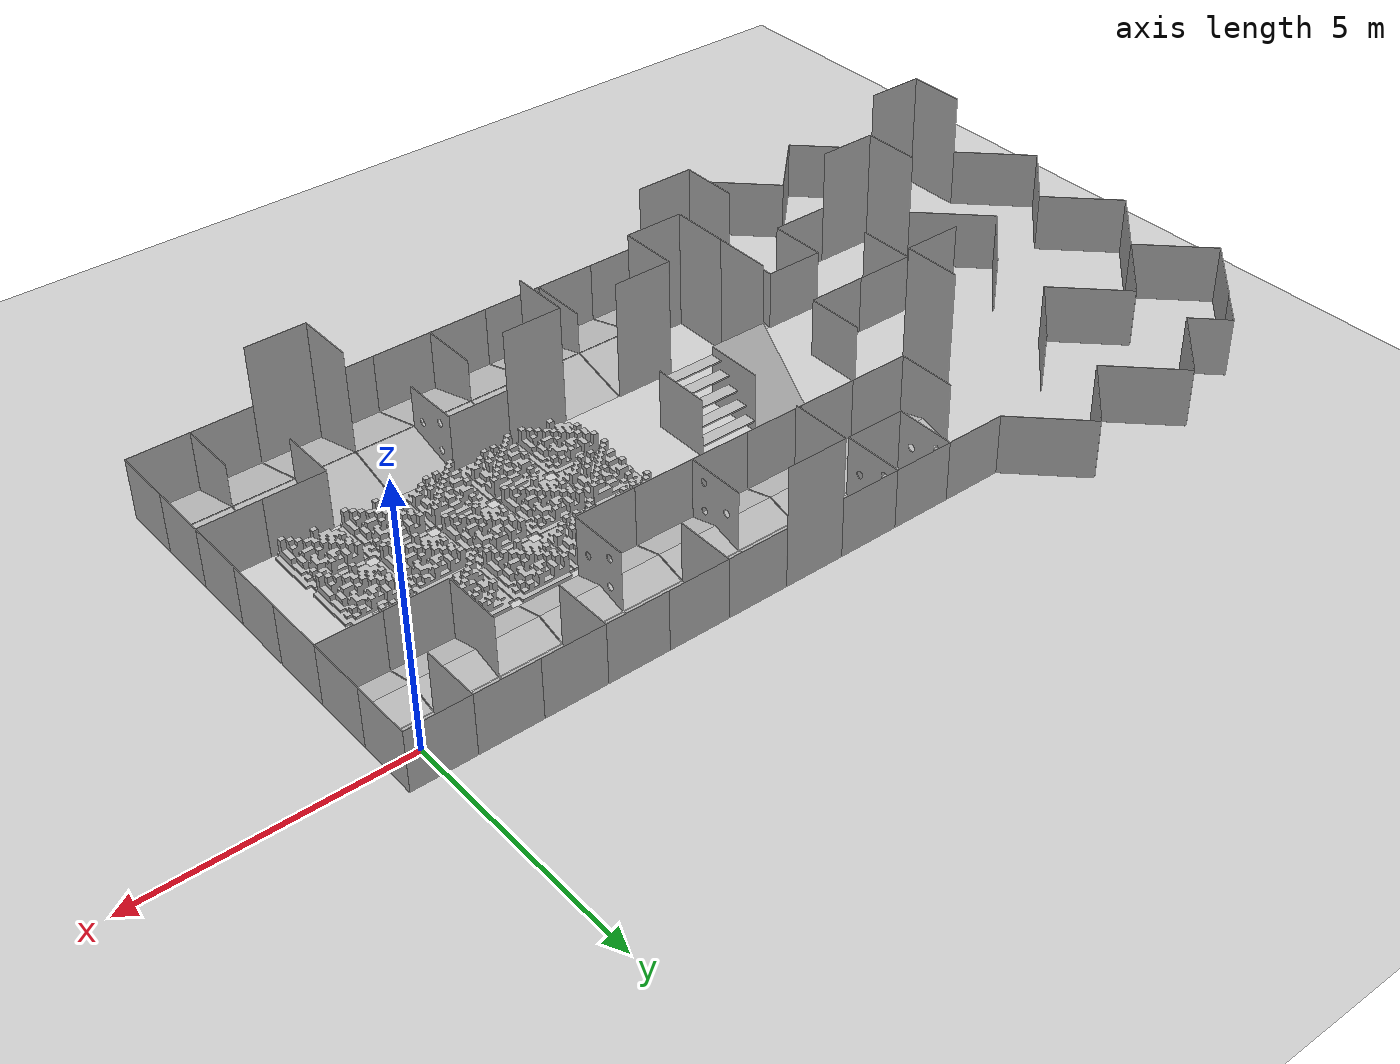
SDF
<sdf version="1.4">
 <world name="default">
  <scene><ambient>0.5 0.5 0.5 1</ambient><background>0.5 0.5 0.5 1</background><shadows>false</shadows></scene>
  <include><uri>model://sun</uri></include>
  <physics type="ode">
   <gravity>0 0 -9.81</gravity>
   <max_step_size>0.001</max_step_size>
   <real_time_factor>1</real_time_factor>
   <real_time_update_rate>1000</real_time_update_rate>
  </physics>
  <light type="directional" name="directional_light_1">
   <cast_shadows>false</cast_shadows>
   <pose>0 0 30 0.1 0.1 0</pose>
   <diffuse>.5 .5 .5 1</diffuse>
   <specular>.1 .1 .1 1</specular>
   <attenuation><range>300</range></attenuation>
   <direction>0.1 0.1 -1</direction>
  </light>
  <model name="plane_model">
   <static>true</static>
   <link name="plane_model_link">
    <collision name="plane_model_collision">
     <geometry><plane><normal>0 0 1</normal><size>40 40</size></plane></geometry>
    </collision>
    <visual name="plane_model_visual">
     <cast_shadows>false</cast_shadows>
     <geometry><plane><normal>0 0 1</normal><size>40 40</size></plane></geometry>
     <material><script>Gazebo/Grey</script></material>
    </visual>
   </link>
  </model>
  <model name="small_wall_1">
   <static>true</static>
   <link name="small_wall_1_link">
    <pose>0 0 0 0 0 -1.5708</pose>
    <collision name="small_wall_1_collision">
     <geometry><mesh><uri>file://robocup/walls/small_wall.dae</uri><scale>1 1 1</scale></mesh></geometry>
    </collision>
    <visual name="small_wall_1_visual">
     <cast_shadows>false</cast_shadows>
     <geometry><mesh><uri>file://robocup/walls/small_wall.dae</uri><scale>1 1 1</scale></mesh></geometry>
    </visual>
   </link>
  </model>
  <model name="small_wall_2">
   <static>true</static>
   <link name="small_wall_2_link">
    <pose>0 1.2 0 0 0 -3.14159</pose>
    <collision name="small_wall_2_collision">
     <geometry><mesh><uri>file://robocup/walls/small_wall.dae</uri><scale>1 1 1</scale></mesh></geometry>
    </collision>
    <visual name="small_wall_2_visual">
     <cast_shadows>false</cast_shadows>
     <geometry><mesh><uri>file://robocup/walls/small_wall.dae</uri><scale>1 1 1</scale></mesh></geometry>
    </visual>
   </link>
  </model>
  <model name="small_wall_3">
   <static>true</static>
   <link name="small_wall_3_link">
    <pose>0 -1.2 0 0 0 -1.5708</pose>
    <collision name="small_wall_3_collision">
     <geometry><mesh><uri>file://robocup/walls/small_wall.dae</uri><scale>1 1 1</scale></mesh></geometry>
    </collision>
    <visual name="small_wall_3_visual">
     <cast_shadows>false</cast_shadows>
     <geometry><mesh><uri>file://robocup/walls/small_wall.dae</uri><scale>1 1 1</scale></mesh></geometry>
    </visual>
   </link>
  </model>
  <model name="small_wall_4">
   <static>true</static>
   <link name="small_wall_4_link">
    <pose>0 -2.4 0 0 0 0</pose>
    <collision name="small_wall_4_collision">
     <geometry><mesh><uri>file://robocup/walls/small_wall.dae</uri><scale>1 1 1</scale></mesh></geometry>
    </collision>
    <visual name="small_wall_4_visual">
     <cast_shadows>false</cast_shadows>
     <geometry><mesh><uri>file://robocup/walls/small_wall.dae</uri><scale>1 1 1</scale></mesh></geometry>
    </visual>
   </link>
  </model>
  <model name="small_wall_5">
   <static>true</static>
   <link name="small_wall_5_link">
    <pose>0 0 0 0 0 -4.71239</pose>
    <collision name="small_wall_5_collision">
     <geometry><mesh><uri>file://robocup/walls/small_wall.dae</uri><scale>1 1 1</scale></mesh></geometry>
    </collision>
    <visual name="small_wall_5_visual">
     <cast_shadows>false</cast_shadows>
     <geometry><mesh><uri>file://robocup/walls/small_wall.dae</uri><scale>1 1 1</scale></mesh></geometry>
    </visual>
   </link>
  </model>
  <model name="small_wall_6">
   <static>true</static>
   <link name="small_wall_6_link">
    <pose>-1.2 0 0 0 0 0</pose>
    <collision name="small_wall_6_collision">
     <geometry><mesh><uri>file://robocup/walls/small_wall.dae</uri><scale>1 1 1</scale></mesh></geometry>
    </collision>
    <visual name="small_wall_6_visual">
     <cast_shadows>false</cast_shadows>
     <geometry><mesh><uri>file://robocup/walls/small_wall.dae</uri><scale>1 1 1</scale></mesh></geometry>
    </visual>
   </link>
  </model>
  <model name="small_wall_7">
   <static>true</static>
   <link name="small_wall_7_link">
    <pose>-2.4 1.2 0 0 0 -3.14159</pose>
    <collision name="small_wall_7_collision">
     <geometry><mesh><uri>file://robocup/walls/small_wall.dae</uri><scale>1 1 1</scale></mesh></geometry>
    </collision>
    <visual name="small_wall_7_visual">
     <cast_shadows>false</cast_shadows>
     <geometry><mesh><uri>file://robocup/walls/small_wall.dae</uri><scale>1 1 1</scale></mesh></geometry>
    </visual>
   </link>
  </model>
  <model name="small_wall_8">
   <static>true</static>
   <link name="small_wall_8_link">
    <pose>-3.6 0 0 0 0 0</pose>
    <collision name="small_wall_8_collision">
     <geometry><mesh><uri>file://robocup/walls/small_wall.dae</uri><scale>1 1 1</scale></mesh></geometry>
    </collision>
    <visual name="small_wall_8_visual">
     <cast_shadows>false</cast_shadows>
     <geometry><mesh><uri>file://robocup/walls/small_wall.dae</uri><scale>1 1 1</scale></mesh></geometry>
    </visual>
   </link>
  </model>
  <model name="half_ramp_1">
   <static>true</static>
   <link name="half_ramp_1_link">
    <collision name="half_ramp_1_collision">
     <geometry><mesh><uri>file://robocup/ramps/half_ramp.dae</uri><scale>1 1 1</scale></mesh></geometry>
    </collision>
    <visual name="half_ramp_1_visual">
     <cast_shadows>false</cast_shadows>
     <geometry><mesh><uri>file://robocup/ramps/half_ramp.dae</uri><scale>1 1 1</scale></mesh></geometry>
    </visual>
   </link>
  </model>
  <model name="half_ramp_2">
   <static>true</static>
   <link name="half_ramp_2_link">
    <pose>0 -1.2 0 0 0 0</pose>
    <collision name="half_ramp_2_collision">
     <geometry><mesh><uri>file://robocup/ramps/half_ramp.dae</uri><scale>1 1 1</scale></mesh></geometry>
    </collision>
    <visual name="half_ramp_2_visual">
     <cast_shadows>false</cast_shadows>
     <geometry><mesh><uri>file://robocup/ramps/half_ramp.dae</uri><scale>1 1 1</scale></mesh></geometry>
    </visual>
   </link>
  </model>
  <model name="half_ramp_3">
   <static>true</static>
   <link name="half_ramp_3_link">
    <pose>-1.2 0 0 0 0 -3.14159</pose>
    <collision name="half_ramp_3_collision">
     <geometry><mesh><uri>file://robocup/ramps/half_ramp.dae</uri><scale>1 1 1</scale></mesh></geometry>
    </collision>
    <visual name="half_ramp_3_visual">
     <cast_shadows>false</cast_shadows>
     <geometry><mesh><uri>file://robocup/ramps/half_ramp.dae</uri><scale>1 1 1</scale></mesh></geometry>
    </visual>
   </link>
  </model>
  <model name="half_ramp_4">
   <static>true</static>
   <link name="half_ramp_4_link">
    <pose>-1.2 -1.2 0 0 0 0</pose>
    <collision name="half_ramp_4_collision">
     <geometry><mesh><uri>file://robocup/ramps/half_ramp.dae</uri><scale>1 1 1</scale></mesh></geometry>
    </collision>
    <visual name="half_ramp_4_visual">
     <cast_shadows>false</cast_shadows>
     <geometry><mesh><uri>file://robocup/ramps/half_ramp.dae</uri><scale>1 1 1</scale></mesh></geometry>
    </visual>
   </link>
  </model>
  <model name="half_ramp_5">
   <static>true</static>
   <link name="half_ramp_5_link">
    <pose>-2.4 0 0 0 0 0</pose>
    <collision name="half_ramp_5_collision">
     <geometry><mesh><uri>file://robocup/ramps/half_ramp.dae</uri><scale>1 1 1</scale></mesh></geometry>
    </collision>
    <visual name="half_ramp_5_visual">
     <cast_shadows>false</cast_shadows>
     <geometry><mesh><uri>file://robocup/ramps/half_ramp.dae</uri><scale>1 1 1</scale></mesh></geometry>
    </visual>
   </link>
  </model>
  <model name="half_ramp_6">
   <static>true</static>
   <link name="half_ramp_6_link">
    <pose>-2.4 0 0 0 0 -3.14159</pose>
    <collision name="half_ramp_6_collision">
     <geometry><mesh><uri>file://robocup/ramps/half_ramp.dae</uri><scale>1 1 1</scale></mesh></geometry>
    </collision>
    <visual name="half_ramp_6_visual">
     <cast_shadows>false</cast_shadows>
     <geometry><mesh><uri>file://robocup/ramps/half_ramp.dae</uri><scale>1 1 1</scale></mesh></geometry>
    </visual>
   </link>
  </model>
  <model name="half_ramp_7">
   <static>true</static>
   <link name="half_ramp_7_link">
    <pose>-1.2 0 0 0 0 0</pose>
    <collision name="half_ramp_7_collision">
     <geometry><mesh><uri>file://robocup/ramps/half_ramp.dae</uri><scale>1 1 1</scale></mesh></geometry>
    </collision>
    <visual name="half_ramp_7_visual">
     <cast_shadows>false</cast_shadows>
     <geometry><mesh><uri>file://robocup/ramps/half_ramp.dae</uri><scale>1 1 1</scale></mesh></geometry>
    </visual>
   </link>
  </model>
  <model name="half_ramp_8">
   <static>true</static>
   <link name="half_ramp_8_link">
    <pose>0 0 0 0 0 -3.14159</pose>
    <collision name="half_ramp_8_collision">
     <geometry><mesh><uri>file://robocup/ramps/half_ramp.dae</uri><scale>1 1 1</scale></mesh></geometry>
    </collision>
    <visual name="half_ramp_8_visual">
     <cast_shadows>false</cast_shadows>
     <geometry><mesh><uri>file://robocup/ramps/half_ramp.dae</uri><scale>1 1 1</scale></mesh></geometry>
    </visual>
   </link>
  </model>
  <model name="half_ramp_9">
   <static>true</static>
   <link name="half_ramp_9_link">
    <pose>0 -1.2 0 0 0 -3.14159</pose>
    <collision name="half_ramp_9_collision">
     <geometry><mesh><uri>file://robocup/ramps/half_ramp.dae</uri><scale>1 1 1</scale></mesh></geometry>
    </collision>
    <visual name="half_ramp_9_visual">
     <cast_shadows>false</cast_shadows>
     <geometry><mesh><uri>file://robocup/ramps/half_ramp.dae</uri><scale>1 1 1</scale></mesh></geometry>
    </visual>
   </link>
  </model>
  <model name="half_ramp_10">
   <static>true</static>
   <link name="half_ramp_10_link">
    <pose>-1.2 -1.2 0 0 0 -3.14159</pose>
    <collision name="half_ramp_10_collision">
     <geometry><mesh><uri>file://robocup/ramps/half_ramp.dae</uri><scale>1 1 1</scale></mesh></geometry>
    </collision>
    <visual name="half_ramp_10_visual">
     <cast_shadows>false</cast_shadows>
     <geometry><mesh><uri>file://robocup/ramps/half_ramp.dae</uri><scale>1 1 1</scale></mesh></geometry>
    </visual>
   </link>
  </model>
  <model name="small_wall_9">
   <static>true</static>
   <link name="small_wall_9_link">
    <pose>-1.2 -2.4 0 0 0 0</pose>
    <collision name="small_wall_9_collision">
     <geometry><mesh><uri>file://robocup/walls/small_wall.dae</uri><scale>1 1 1</scale></mesh></geometry>
    </collision>
    <visual name="small_wall_9_visual">
     <cast_shadows>false</cast_shadows>
     <geometry><mesh><uri>file://robocup/walls/small_wall.dae</uri><scale>1 1 1</scale></mesh></geometry>
    </visual>
   </link>
  </model>
  <model name="small_wall_10">
   <static>true</static>
   <link name="small_wall_10_link">
    <pose>-1.2 -1.2 0 0 0 -4.71239</pose>
    <collision name="small_wall_10_collision">
     <geometry><mesh><uri>file://robocup/walls/small_wall.dae</uri><scale>1 1 1</scale></mesh></geometry>
    </collision>
    <visual name="small_wall_10_visual">
     <cast_shadows>false</cast_shadows>
     <geometry><mesh><uri>file://robocup/walls/small_wall.dae</uri><scale>1 1 1</scale></mesh></geometry>
    </visual>
   </link>
  </model>
  <model name="small_wall_13">
   <static>true</static>
   <link name="small_wall_13_link">
    <pose>-2.4 0 0 0 0 -4.71239</pose>
    <collision name="small_wall_13_collision">
     <geometry><mesh><uri>file://robocup/walls/small_wall.dae</uri><scale>1 1 1</scale></mesh></geometry>
    </collision>
    <visual name="small_wall_13_visual">
     <cast_shadows>false</cast_shadows>
     <geometry><mesh><uri>file://robocup/walls/small_wall.dae</uri><scale>1 1 1</scale></mesh></geometry>
    </visual>
   </link>
  </model>
  <model name="small_wall_14">
   <static>true</static>
   <link name="small_wall_14_link">
    <pose>-4.8 0 0 0 0 0</pose>
    <collision name="small_wall_14_collision">
     <geometry><mesh><uri>file://robocup/walls/small_wall.dae</uri><scale>1 1 1</scale></mesh></geometry>
    </collision>
    <visual name="small_wall_14_visual">
     <cast_shadows>false</cast_shadows>
     <geometry><mesh><uri>file://robocup/walls/small_wall.dae</uri><scale>1 1 1</scale></mesh></geometry>
    </visual>
   </link>
  </model>
  <model name="small_wall_15">
   <static>true</static>
   <link name="small_wall_15_link">
    <pose>-6 0 0 0 0 0</pose>
    <collision name="small_wall_15_collision">
     <geometry><mesh><uri>file://robocup/walls/small_wall.dae</uri><scale>1 1 1</scale></mesh></geometry>
    </collision>
    <visual name="small_wall_15_visual">
     <cast_shadows>false</cast_shadows>
     <geometry><mesh><uri>file://robocup/walls/small_wall.dae</uri><scale>1 1 1</scale></mesh></geometry>
    </visual>
   </link>
  </model>
  <model name="small_wall_16">
   <static>true</static>
   <link name="small_wall_16_link">
    <pose>-4.8 -1.2 0 0 0 -3.14159</pose>
    <collision name="small_wall_16_collision">
     <geometry><mesh><uri>file://robocup/walls/small_wall.dae</uri><scale>1 1 1</scale></mesh></geometry>
    </collision>
    <visual name="small_wall_16_visual">
     <cast_shadows>false</cast_shadows>
     <geometry><mesh><uri>file://robocup/walls/small_wall.dae</uri><scale>1 1 1</scale></mesh></geometry>
    </visual>
   </link>
  </model>
  <model name="small_wall_17">
   <static>true</static>
   <link name="small_wall_17_link">
    <pose>-6 -1.2 0 0 0 -3.14159</pose>
    <collision name="small_wall_17_collision">
     <geometry><mesh><uri>file://robocup/walls/small_wall.dae</uri><scale>1 1 1</scale></mesh></geometry>
    </collision>
    <visual name="small_wall_17_visual">
     <cast_shadows>false</cast_shadows>
     <geometry><mesh><uri>file://robocup/walls/small_wall.dae</uri><scale>1 1 1</scale></mesh></geometry>
    </visual>
   </link>
  </model>
  <model name="small_wall_18">
   <static>true</static>
   <link name="small_wall_18_link">
    <pose>-4.8 0 0 0 0 -4.71239</pose>
    <collision name="small_wall_18_collision">
     <geometry><mesh><uri>file://robocup/walls/small_wall.dae</uri><scale>1 1 1</scale></mesh></geometry>
    </collision>
    <visual name="small_wall_18_visual">
     <cast_shadows>false</cast_shadows>
     <geometry><mesh><uri>file://robocup/walls/small_wall.dae</uri><scale>1 1 1</scale></mesh></geometry>
    </visual>
   </link>
  </model>
  <model name="small_wall_19">
   <static>true</static>
   <link name="small_wall_19_link">
    <pose>-7.2 -2.4 0 0 0 0</pose>
    <collision name="small_wall_19_collision">
     <geometry><mesh><uri>file://robocup/walls/small_wall.dae</uri><scale>1 1 1</scale></mesh></geometry>
    </collision>
    <visual name="small_wall_19_visual">
     <cast_shadows>false</cast_shadows>
     <geometry><mesh><uri>file://robocup/walls/small_wall.dae</uri><scale>1 1 1</scale></mesh></geometry>
    </visual>
   </link>
  </model>
  <model name="tall_wall_1">
   <static>true</static>
   <link name="tall_wall_1_link">
    <pose>-7.2 1.2 0 0 0 -3.14159</pose>
    <collision name="tall_wall_1_collision">
     <geometry><mesh><uri>file://robocup/walls/tall_wall.dae</uri><scale>1 1 1</scale></mesh></geometry>
    </collision>
    <visual name="tall_wall_1_visual">
     <cast_shadows>false</cast_shadows>
     <geometry><mesh><uri>file://robocup/walls/tall_wall.dae</uri><scale>1 1 1</scale></mesh></geometry>
    </visual>
   </link>
  </model>
  <model name="tall_wall_2">
   <static>true</static>
   <link name="tall_wall_2_link">
    <pose>-8.4 0 0 0 0 -1.5708</pose>
    <collision name="tall_wall_2_collision">
     <geometry><mesh><uri>file://robocup/walls/tall_wall.dae</uri><scale>1 1 1</scale></mesh></geometry>
    </collision>
    <visual name="tall_wall_2_visual">
     <cast_shadows>false</cast_shadows>
     <geometry><mesh><uri>file://robocup/walls/tall_wall.dae</uri><scale>1 1 1</scale></mesh></geometry>
    </visual>
   </link>
  </model>
  <model name="small_wall_20">
   <static>true</static>
   <link name="small_wall_20_link">
    <pose>-8.4 -1.2 0 0 0 -3.14159</pose>
    <collision name="small_wall_20_collision">
     <geometry><mesh><uri>file://robocup/walls/small_wall.dae</uri><scale>1 1 1</scale></mesh></geometry>
    </collision>
    <visual name="small_wall_20_visual">
     <cast_shadows>false</cast_shadows>
     <geometry><mesh><uri>file://robocup/walls/small_wall.dae</uri><scale>1 1 1</scale></mesh></geometry>
    </visual>
   </link>
  </model>
  <model name="small_wall_21">
   <static>true</static>
   <link name="small_wall_21_link">
    <pose>-8.4 1.2 0 0 0 -3.14159</pose>
    <collision name="small_wall_21_collision">
     <geometry><mesh><uri>file://robocup/walls/small_wall.dae</uri><scale>1 1 1</scale></mesh></geometry>
    </collision>
    <visual name="small_wall_21_visual">
     <cast_shadows>false</cast_shadows>
     <geometry><mesh><uri>file://robocup/walls/small_wall.dae</uri><scale>1 1 1</scale></mesh></geometry>
    </visual>
   </link>
  </model>
  <model name="small_wall_22">
   <static>true</static>
   <link name="small_wall_22_link">
    <pose>-9.6 1.2 0 0 0 -3.14159</pose>
    <collision name="small_wall_22_collision">
     <geometry><mesh><uri>file://robocup/walls/small_wall.dae</uri><scale>1 1 1</scale></mesh></geometry>
    </collision>
    <visual name="small_wall_22_visual">
     <cast_shadows>false</cast_shadows>
     <geometry><mesh><uri>file://robocup/walls/small_wall.dae</uri><scale>1 1 1</scale></mesh></geometry>
    </visual>
   </link>
  </model>
  <model name="small_wall_23">
   <static>true</static>
   <link name="small_wall_23_link">
    <pose>-10.8 0 0 0 0 0</pose>
    <collision name="small_wall_23_collision">
     <geometry><mesh><uri>file://robocup/walls/small_wall.dae</uri><scale>1 1 1</scale></mesh></geometry>
    </collision>
    <visual name="small_wall_23_visual">
     <cast_shadows>false</cast_shadows>
     <geometry><mesh><uri>file://robocup/walls/small_wall.dae</uri><scale>1 1 1</scale></mesh></geometry>
    </visual>
   </link>
  </model>
  <model name="small_wall_24">
   <static>true</static>
   <link name="small_wall_24_link">
    <pose>-9.6 -1.2 0 0 0 -3.14159</pose>
    <collision name="small_wall_24_collision">
     <geometry><mesh><uri>file://robocup/walls/small_wall.dae</uri><scale>1 1 1</scale></mesh></geometry>
    </collision>
    <visual name="small_wall_24_visual">
     <cast_shadows>false</cast_shadows>
     <geometry><mesh><uri>file://robocup/walls/small_wall.dae</uri><scale>1 1 1</scale></mesh></geometry>
    </visual>
   </link>
  </model>
  <model name="small_wall_25">
   <static>true</static>
   <link name="small_wall_25_link">
    <pose>-10.8 -2.4 0 0 0 0</pose>
    <collision name="small_wall_25_collision">
     <geometry><mesh><uri>file://robocup/walls/small_wall.dae</uri><scale>1 1 1</scale></mesh></geometry>
    </collision>
    <visual name="small_wall_25_visual">
     <cast_shadows>false</cast_shadows>
     <geometry><mesh><uri>file://robocup/walls/small_wall.dae</uri><scale>1 1 1</scale></mesh></geometry>
    </visual>
   </link>
  </model>
  <model name="half_ramp_11">
   <static>true</static>
   <link name="half_ramp_11_link">
    <pose>-3.6 0 0 0 0 0</pose>
    <collision name="half_ramp_11_collision">
     <geometry><mesh><uri>file://robocup/ramps/half_ramp.dae</uri><scale>1 1 1</scale></mesh></geometry>
    </collision>
    <visual name="half_ramp_11_visual">
     <cast_shadows>false</cast_shadows>
     <geometry><mesh><uri>file://robocup/ramps/half_ramp.dae</uri><scale>1 1 1</scale></mesh></geometry>
    </visual>
   </link>
  </model>
  <model name="half_ramp_12">
   <static>true</static>
   <link name="half_ramp_12_link">
    <pose>-4.8 0 0 0 0 0</pose>
    <collision name="half_ramp_12_collision">
     <geometry><mesh><uri>file://robocup/ramps/half_ramp.dae</uri><scale>1 1 1</scale></mesh></geometry>
    </collision>
    <visual name="half_ramp_12_visual">
     <cast_shadows>false</cast_shadows>
     <geometry><mesh><uri>file://robocup/ramps/half_ramp.dae</uri><scale>1 1 1</scale></mesh></geometry>
    </visual>
   </link>
  </model>
  <model name="half_ramp_13">
   <static>true</static>
   <link name="half_ramp_13_link">
    <pose>-6 0 0 0 0 0</pose>
    <collision name="half_ramp_13_collision">
     <geometry><mesh><uri>file://robocup/ramps/half_ramp.dae</uri><scale>1 1 1</scale></mesh></geometry>
    </collision>
    <visual name="half_ramp_13_visual">
     <cast_shadows>false</cast_shadows>
     <geometry><mesh><uri>file://robocup/ramps/half_ramp.dae</uri><scale>1 1 1</scale></mesh></geometry>
    </visual>
   </link>
  </model>
  <model name="half_ramp_14">
   <static>true</static>
   <link name="half_ramp_14_link">
    <pose>-7.2 0 0 0 0 0</pose>
    <collision name="half_ramp_14_collision">
     <geometry><mesh><uri>file://robocup/ramps/half_ramp.dae</uri><scale>1 1 1</scale></mesh></geometry>
    </collision>
    <visual name="half_ramp_14_visual">
     <cast_shadows>false</cast_shadows>
     <geometry><mesh><uri>file://robocup/ramps/half_ramp.dae</uri><scale>1 1 1</scale></mesh></geometry>
    </visual>
   </link>
  </model>
  <model name="half_ramp_15">
   <static>true</static>
   <link name="half_ramp_15_link">
    <pose>-8.4 0 0 0 0 0</pose>
    <collision name="half_ramp_15_collision">
     <geometry><mesh><uri>file://robocup/ramps/half_ramp.dae</uri><scale>1 1 1</scale></mesh></geometry>
    </collision>
    <visual name="half_ramp_15_visual">
     <cast_shadows>false</cast_shadows>
     <geometry><mesh><uri>file://robocup/ramps/half_ramp.dae</uri><scale>1 1 1</scale></mesh></geometry>
    </visual>
   </link>
  </model>
  <model name="half_ramp_16">
   <static>true</static>
   <link name="half_ramp_16_link">
    <pose>-9.6 0 0 0 0 0</pose>
    <collision name="half_ramp_16_collision">
     <geometry><mesh><uri>file://robocup/ramps/half_ramp.dae</uri><scale>1 1 1</scale></mesh></geometry>
    </collision>
    <visual name="half_ramp_16_visual">
     <cast_shadows>false</cast_shadows>
     <geometry><mesh><uri>file://robocup/ramps/half_ramp.dae</uri><scale>1 1 1</scale></mesh></geometry>
    </visual>
   </link>
  </model>
  <model name="half_ramp_17">
   <static>true</static>
   <link name="half_ramp_17_link">
    <pose>-10.8 0 0 0 0 0</pose>
    <collision name="half_ramp_17_collision">
     <geometry><mesh><uri>file://robocup/ramps/half_ramp.dae</uri><scale>1 1 1</scale></mesh></geometry>
    </collision>
    <visual name="half_ramp_17_visual">
     <cast_shadows>false</cast_shadows>
     <geometry><mesh><uri>file://robocup/ramps/half_ramp.dae</uri><scale>1 1 1</scale></mesh></geometry>
    </visual>
   </link>
  </model>
  <model name="half_ramp_18">
   <static>true</static>
   <link name="half_ramp_18_link">
    <pose>-3.6 -1.2 0 0 0 0</pose>
    <collision name="half_ramp_18_collision">
     <geometry><mesh><uri>file://robocup/ramps/half_ramp.dae</uri><scale>1 1 1</scale></mesh></geometry>
    </collision>
    <visual name="half_ramp_18_visual">
     <cast_shadows>false</cast_shadows>
     <geometry><mesh><uri>file://robocup/ramps/half_ramp.dae</uri><scale>1 1 1</scale></mesh></geometry>
    </visual>
   </link>
  </model>
  <model name="half_ramp_19">
   <static>true</static>
   <link name="half_ramp_19_link">
    <pose>-4.8 -1.2 0 0 0 0</pose>
    <collision name="half_ramp_19_collision">
     <geometry><mesh><uri>file://robocup/ramps/half_ramp.dae</uri><scale>1 1 1</scale></mesh></geometry>
    </collision>
    <visual name="half_ramp_19_visual">
     <cast_shadows>false</cast_shadows>
     <geometry><mesh><uri>file://robocup/ramps/half_ramp.dae</uri><scale>1 1 1</scale></mesh></geometry>
    </visual>
   </link>
  </model>
  <model name="half_ramp_20">
   <static>true</static>
   <link name="half_ramp_20_link">
    <pose>-6 -1.2 0 0 0 0</pose>
    <collision name="half_ramp_20_collision">
     <geometry><mesh><uri>file://robocup/ramps/half_ramp.dae</uri><scale>1 1 1</scale></mesh></geometry>
    </collision>
    <visual name="half_ramp_20_visual">
     <cast_shadows>false</cast_shadows>
     <geometry><mesh><uri>file://robocup/ramps/half_ramp.dae</uri><scale>1 1 1</scale></mesh></geometry>
    </visual>
   </link>
  </model>
  <model name="half_ramp_21">
   <static>true</static>
   <link name="half_ramp_21_link">
    <pose>-7.2 -1.2 0 0 0 0</pose>
    <collision name="half_ramp_21_collision">
     <geometry><mesh><uri>file://robocup/ramps/half_ramp.dae</uri><scale>1 1 1</scale></mesh></geometry>
    </collision>
    <visual name="half_ramp_21_visual">
     <cast_shadows>false</cast_shadows>
     <geometry><mesh><uri>file://robocup/ramps/half_ramp.dae</uri><scale>1 1 1</scale></mesh></geometry>
    </visual>
   </link>
  </model>
  <model name="half_ramp_22">
   <static>true</static>
   <link name="half_ramp_22_link">
    <pose>-8.4 -1.2 0 0 0 0</pose>
    <collision name="half_ramp_22_collision">
     <geometry><mesh><uri>file://robocup/ramps/half_ramp.dae</uri><scale>1 1 1</scale></mesh></geometry>
    </collision>
    <visual name="half_ramp_22_visual">
     <cast_shadows>false</cast_shadows>
     <geometry><mesh><uri>file://robocup/ramps/half_ramp.dae</uri><scale>1 1 1</scale></mesh></geometry>
    </visual>
   </link>
  </model>
  <model name="half_ramp_23">
   <static>true</static>
   <link name="half_ramp_23_link">
    <pose>-9.6 -1.2 0 0 0 0</pose>
    <collision name="half_ramp_23_collision">
     <geometry><mesh><uri>file://robocup/ramps/half_ramp.dae</uri><scale>1 1 1</scale></mesh></geometry>
    </collision>
    <visual name="half_ramp_23_visual">
     <cast_shadows>false</cast_shadows>
     <geometry><mesh><uri>file://robocup/ramps/half_ramp.dae</uri><scale>1 1 1</scale></mesh></geometry>
    </visual>
   </link>
  </model>
  <model name="half_ramp_24">
   <static>true</static>
   <link name="half_ramp_24_link">
    <pose>-10.8 -1.2 0 0 0 0</pose>
    <collision name="half_ramp_24_collision">
     <geometry><mesh><uri>file://robocup/ramps/half_ramp.dae</uri><scale>1 1 1</scale></mesh></geometry>
    </collision>
    <visual name="half_ramp_24_visual">
     <cast_shadows>false</cast_shadows>
     <geometry><mesh><uri>file://robocup/ramps/half_ramp.dae</uri><scale>1 1 1</scale></mesh></geometry>
    </visual>
   </link>
  </model>
  <model name="half_ramp_25">
   <static>true</static>
   <link name="half_ramp_25_link">
    <pose>-10.8 0 0 0 0 -3.14159</pose>
    <collision name="half_ramp_25_collision">
     <geometry><mesh><uri>file://robocup/ramps/half_ramp.dae</uri><scale>1 1 1</scale></mesh></geometry>
    </collision>
    <visual name="half_ramp_25_visual">
     <cast_shadows>false</cast_shadows>
     <geometry><mesh><uri>file://robocup/ramps/half_ramp.dae</uri><scale>1 1 1</scale></mesh></geometry>
    </visual>
   </link>
  </model>
  <model name="half_ramp_26">
   <static>true</static>
   <link name="half_ramp_26_link">
    <pose>-10.8 -1.2 0 0 0 -3.14159</pose>
    <collision name="half_ramp_26_collision">
     <geometry><mesh><uri>file://robocup/ramps/half_ramp.dae</uri><scale>1 1 1</scale></mesh></geometry>
    </collision>
    <visual name="half_ramp_26_visual">
     <cast_shadows>false</cast_shadows>
     <geometry><mesh><uri>file://robocup/ramps/half_ramp.dae</uri><scale>1 1 1</scale></mesh></geometry>
    </visual>
   </link>
  </model>
  <model name="half_ramp_27">
   <static>true</static>
   <link name="half_ramp_27_link">
    <pose>-9.6 -1.2 0 0 0 -3.14159</pose>
    <collision name="half_ramp_27_collision">
     <geometry><mesh><uri>file://robocup/ramps/half_ramp.dae</uri><scale>1 1 1</scale></mesh></geometry>
    </collision>
    <visual name="half_ramp_27_visual">
     <cast_shadows>false</cast_shadows>
     <geometry><mesh><uri>file://robocup/ramps/half_ramp.dae</uri><scale>1 1 1</scale></mesh></geometry>
    </visual>
   </link>
  </model>
  <model name="half_ramp_28">
   <static>true</static>
   <link name="half_ramp_28_link">
    <pose>-8.4 -1.2 0 0 0 -3.14159</pose>
    <collision name="half_ramp_28_collision">
     <geometry><mesh><uri>file://robocup/ramps/half_ramp.dae</uri><scale>1 1 1</scale></mesh></geometry>
    </collision>
    <visual name="half_ramp_28_visual">
     <cast_shadows>false</cast_shadows>
     <geometry><mesh><uri>file://robocup/ramps/half_ramp.dae</uri><scale>1 1 1</scale></mesh></geometry>
    </visual>
   </link>
  </model>
  <model name="half_ramp_29">
   <static>true</static>
   <link name="half_ramp_29_link">
    <pose>-7.2 -1.2 0 0 0 -3.14159</pose>
    <collision name="half_ramp_29_collision">
     <geometry><mesh><uri>file://robocup/ramps/half_ramp.dae</uri><scale>1 1 1</scale></mesh></geometry>
    </collision>
    <visual name="half_ramp_29_visual">
     <cast_shadows>false</cast_shadows>
     <geometry><mesh><uri>file://robocup/ramps/half_ramp.dae</uri><scale>1 1 1</scale></mesh></geometry>
    </visual>
   </link>
  </model>
  <model name="half_ramp_30">
   <static>true</static>
   <link name="half_ramp_30_link">
    <pose>-9.6 0 0 0 0 -3.14159</pose>
    <collision name="half_ramp_30_collision">
     <geometry><mesh><uri>file://robocup/ramps/half_ramp.dae</uri><scale>1 1 1</scale></mesh></geometry>
    </collision>
    <visual name="half_ramp_30_visual">
     <cast_shadows>false</cast_shadows>
     <geometry><mesh><uri>file://robocup/ramps/half_ramp.dae</uri><scale>1 1 1</scale></mesh></geometry>
    </visual>
   </link>
  </model>
  <model name="half_ramp_31">
   <static>true</static>
   <link name="half_ramp_31_link">
    <pose>-8.4 0 0 0 0 -3.14159</pose>
    <collision name="half_ramp_31_collision">
     <geometry><mesh><uri>file://robocup/ramps/half_ramp.dae</uri><scale>1 1 1</scale></mesh></geometry>
    </collision>
    <visual name="half_ramp_31_visual">
     <cast_shadows>false</cast_shadows>
     <geometry><mesh><uri>file://robocup/ramps/half_ramp.dae</uri><scale>1 1 1</scale></mesh></geometry>
    </visual>
   </link>
  </model>
  <model name="half_ramp_32">
   <static>true</static>
   <link name="half_ramp_32_link">
    <pose>-7.2 0 0 0 0 -3.14159</pose>
    <collision name="half_ramp_32_collision">
     <geometry><mesh><uri>file://robocup/ramps/half_ramp.dae</uri><scale>1 1 1</scale></mesh></geometry>
    </collision>
    <visual name="half_ramp_32_visual">
     <cast_shadows>false</cast_shadows>
     <geometry><mesh><uri>file://robocup/ramps/half_ramp.dae</uri><scale>1 1 1</scale></mesh></geometry>
    </visual>
   </link>
  </model>
  <model name="half_ramp_33">
   <static>true</static>
   <link name="half_ramp_33_link">
    <pose>-6 0 0 0 0 -3.14159</pose>
    <collision name="half_ramp_33_collision">
     <geometry><mesh><uri>file://robocup/ramps/half_ramp.dae</uri><scale>1 1 1</scale></mesh></geometry>
    </collision>
    <visual name="half_ramp_33_visual">
     <cast_shadows>false</cast_shadows>
     <geometry><mesh><uri>file://robocup/ramps/half_ramp.dae</uri><scale>1 1 1</scale></mesh></geometry>
    </visual>
   </link>
  </model>
  <model name="half_ramp_34">
   <static>true</static>
   <link name="half_ramp_34_link">
    <pose>-4.8 0 0 0 0 -3.14159</pose>
    <collision name="half_ramp_34_collision">
     <geometry><mesh><uri>file://robocup/ramps/half_ramp.dae</uri><scale>1 1 1</scale></mesh></geometry>
    </collision>
    <visual name="half_ramp_34_visual">
     <cast_shadows>false</cast_shadows>
     <geometry><mesh><uri>file://robocup/ramps/half_ramp.dae</uri><scale>1 1 1</scale></mesh></geometry>
    </visual>
   </link>
  </model>
  <model name="half_ramp_35">
   <static>true</static>
   <link name="half_ramp_35_link">
    <pose>-3.6 0 0 0 0 -3.14159</pose>
    <collision name="half_ramp_35_collision">
     <geometry><mesh><uri>file://robocup/ramps/half_ramp.dae</uri><scale>1 1 1</scale></mesh></geometry>
    </collision>
    <visual name="half_ramp_35_visual">
     <cast_shadows>false</cast_shadows>
     <geometry><mesh><uri>file://robocup/ramps/half_ramp.dae</uri><scale>1 1 1</scale></mesh></geometry>
    </visual>
   </link>
  </model>
  <model name="half_ramp_36">
   <static>true</static>
   <link name="half_ramp_36_link">
    <pose>-6 -1.2 0 0 0 -3.14159</pose>
    <collision name="half_ramp_36_collision">
     <geometry><mesh><uri>file://robocup/ramps/half_ramp.dae</uri><scale>1 1 1</scale></mesh></geometry>
    </collision>
    <visual name="half_ramp_36_visual">
     <cast_shadows>false</cast_shadows>
     <geometry><mesh><uri>file://robocup/ramps/half_ramp.dae</uri><scale>1 1 1</scale></mesh></geometry>
    </visual>
   </link>
  </model>
  <model name="half_ramp_37">
   <static>true</static>
   <link name="half_ramp_37_link">
    <pose>-3.6 -1.2 0 0 0 -3.14159</pose>
    <collision name="half_ramp_37_collision">
     <geometry><mesh><uri>file://robocup/ramps/half_ramp.dae</uri><scale>1 1 1</scale></mesh></geometry>
    </collision>
    <visual name="half_ramp_37_visual">
     <cast_shadows>false</cast_shadows>
     <geometry><mesh><uri>file://robocup/ramps/half_ramp.dae</uri><scale>1 1 1</scale></mesh></geometry>
    </visual>
   </link>
  </model>
  <model name="half_ramp_38">
   <static>true</static>
   <link name="half_ramp_38_link">
    <pose>-4.8 -1.2 0 0 0 -3.14159</pose>
    <collision name="half_ramp_38_collision">
     <geometry><mesh><uri>file://robocup/ramps/half_ramp.dae</uri><scale>1 1 1</scale></mesh></geometry>
    </collision>
    <visual name="half_ramp_38_visual">
     <cast_shadows>false</cast_shadows>
     <geometry><mesh><uri>file://robocup/ramps/half_ramp.dae</uri><scale>1 1 1</scale></mesh></geometry>
    </visual>
   </link>
  </model>
  <model name="wall_holes1_1">
   <static>true</static>
   <link name="wall_holes1_1_link">
    <pose>-4.8 -1.2 0 0 0 -1.5708</pose>
    <collision name="wall_holes1_1_collision">
     <geometry><mesh><uri>file://robocup/walls/small_wall_holes1.dae</uri><scale>1 1 1</scale></mesh></geometry>
    </collision>
    <visual name="wall_holes1_1_visual">
     <cast_shadows>false</cast_shadows>
     <geometry><mesh><uri>file://robocup/walls/small_wall_holes1.dae</uri><scale>1 1 1</scale></mesh></geometry>
    </visual>
   </link>
  </model>
  <model name="stairs_120_1">
   <static>true</static>
   <link name="stairs_120_1_link">
    <pose>-8.4 -3.6 0 0 0 -3.14159</pose>
    <collision name="stairs_120_1_collision">
     <geometry><mesh><uri>file://robocup/other/stairs_120.dae</uri><scale>1 1 1</scale></mesh></geometry>
    </collision>
    <visual name="stairs_120_1_visual">
     <cast_shadows>false</cast_shadows>
     <geometry><mesh><uri>file://robocup/other/stairs_120.dae</uri><scale>1 1 1</scale></mesh></geometry>
    </visual>
   </link>
  </model>
  <model name="simple_elev_ramp_1">
   <static>true</static>
   <link name="simple_elev_ramp_1_link">
    <pose>-9.6 -3.6 0 0 0 -3.14159</pose>
    <collision name="simple_elev_ramp_1_collision">
     <geometry><mesh><uri>file://robocup/ramps/simple_elev_ramp.dae</uri><scale>1 1 1</scale></mesh></geometry>
    </collision>
    <visual name="simple_elev_ramp_1_visual">
     <cast_shadows>false</cast_shadows>
     <geometry><mesh><uri>file://robocup/ramps/simple_elev_ramp.dae</uri><scale>1 1 1</scale></mesh></geometry>
    </visual>
   </link>
  </model>
  <model name="stepfield_red_diagonal_1">
   <static>true</static>
   <link name="stepfield_red_diagonal_1_link">
    <pose>-6 -3.6 0 0 0 0</pose>
    <collision name="stepfield_red_diagonal_1_collision">
     <geometry>
      <mesh><uri>file://robocup/other/stepfield_red_diagonal.dae</uri><scale>1 1 1</scale></mesh>
     </geometry>
    </collision>
    <visual name="stepfield_red_diagonal_1_visual">
     <cast_shadows>false</cast_shadows>
     <geometry>
      <mesh><uri>file://robocup/other/stepfield_red_diagonal.dae</uri><scale>1 1 1</scale></mesh>
     </geometry>
    </visual>
   </link>
  </model>
  <model name="stepfield_red_diagonal_2">
   <static>true</static>
   <link name="stepfield_red_diagonal_2_link">
    <pose>-4.8 -4.8 0 0 0 0</pose>
    <collision name="stepfield_red_diagonal_2_collision">
     <geometry>
      <mesh><uri>file://robocup/other/stepfield_red_diagonal.dae</uri><scale>1 1 1</scale></mesh>
     </geometry>
    </collision>
    <visual name="stepfield_red_diagonal_2_visual">
     <cast_shadows>false</cast_shadows>
     <geometry>
      <mesh><uri>file://robocup/other/stepfield_red_diagonal.dae</uri><scale>1 1 1</scale></mesh>
     </geometry>
    </visual>
   </link>
  </model>
  <model name="stepfield_red_diagonal_3">
   <static>true</static>
   <link name="stepfield_red_diagonal_3_link">
    <pose>-4.8 -3.6 0 0 0 -1.5708</pose>
    <collision name="stepfield_red_diagonal_3_collision">
     <geometry>
      <mesh><uri>file://robocup/other/stepfield_red_diagonal.dae</uri><scale>1 1 1</scale></mesh>
     </geometry>
    </collision>
    <visual name="stepfield_red_diagonal_3_visual">
     <cast_shadows>false</cast_shadows>
     <geometry>
      <mesh><uri>file://robocup/other/stepfield_red_diagonal.dae</uri><scale>1 1 1</scale></mesh>
     </geometry>
    </visual>
   </link>
  </model>
  <model name="stepfield_red_diagonal_4">
   <static>true</static>
   <link name="stepfield_red_diagonal_4_link">
    <pose>-6 -4.8 0 0 0 -1.5708</pose>
    <collision name="stepfield_red_diagonal_4_collision">
     <geometry>
      <mesh><uri>file://robocup/other/stepfield_red_diagonal.dae</uri><scale>1 1 1</scale></mesh>
     </geometry>
    </collision>
    <visual name="stepfield_red_diagonal_4_visual">
     <cast_shadows>false</cast_shadows>
     <geometry>
      <mesh><uri>file://robocup/other/stepfield_red_diagonal.dae</uri><scale>1 1 1</scale></mesh>
     </geometry>
    </visual>
   </link>
  </model>
  <model name="stepfield_red_diagonal_5">
   <static>true</static>
   <link name="stepfield_red_diagonal_5_link">
    <pose>-3.6 -3.6 0 0 0 -1.5708</pose>
    <collision name="stepfield_red_diagonal_5_collision">
     <geometry>
      <mesh><uri>file://robocup/other/stepfield_red_diagonal.dae</uri><scale>1 1 1</scale></mesh>
     </geometry>
    </collision>
    <visual name="stepfield_red_diagonal_5_visual">
     <cast_shadows>false</cast_shadows>
     <geometry>
      <mesh><uri>file://robocup/other/stepfield_red_diagonal.dae</uri><scale>1 1 1</scale></mesh>
     </geometry>
    </visual>
   </link>
  </model>
  <model name="stepfield_red_diagonal_6">
   <static>true</static>
   <link name="stepfield_red_diagonal_6_link">
    <pose>-3.6 -4.8 0 0 0 0</pose>
    <collision name="stepfield_red_diagonal_6_collision">
     <geometry>
      <mesh><uri>file://robocup/other/stepfield_red_diagonal.dae</uri><scale>1 1 1</scale></mesh>
     </geometry>
    </collision>
    <visual name="stepfield_red_diagonal_6_visual">
     <cast_shadows>false</cast_shadows>
     <geometry>
      <mesh><uri>file://robocup/other/stepfield_red_diagonal.dae</uri><scale>1 1 1</scale></mesh>
     </geometry>
    </visual>
   </link>
  </model>
  <model name="stepfield_red_diagonal_7">
   <static>true</static>
   <link name="stepfield_red_diagonal_7_link">
    <pose>-2.4 -3.6 0 0 0 -1.5708</pose>
    <collision name="stepfield_red_diagonal_7_collision">
     <geometry>
      <mesh><uri>file://robocup/other/stepfield_red_diagonal.dae</uri><scale>1 1 1</scale></mesh>
     </geometry>
    </collision>
    <visual name="stepfield_red_diagonal_7_visual">
     <cast_shadows>false</cast_shadows>
     <geometry>
      <mesh><uri>file://robocup/other/stepfield_red_diagonal.dae</uri><scale>1 1 1</scale></mesh>
     </geometry>
    </visual>
   </link>
  </model>
  <model name="stepfield_red_diagonal_8">
   <static>true</static>
   <link name="stepfield_red_diagonal_8_link">
    <pose>-1.2 -3.6 0 0 0 -1.5708</pose>
    <collision name="stepfield_red_diagonal_8_collision">
     <geometry>
      <mesh><uri>file://robocup/other/stepfield_red_diagonal.dae</uri><scale>1 1 1</scale></mesh>
     </geometry>
    </collision>
    <visual name="stepfield_red_diagonal_8_visual">
     <cast_shadows>false</cast_shadows>
     <geometry>
      <mesh><uri>file://robocup/other/stepfield_red_diagonal.dae</uri><scale>1 1 1</scale></mesh>
     </geometry>
    </visual>
   </link>
  </model>
  <model name="stepfield_red_diagonal_9">
   <static>true</static>
   <link name="stepfield_red_diagonal_9_link">
    <pose>-1.2 -4.8 0 0 0 -1.5708</pose>
    <collision name="stepfield_red_diagonal_9_collision">
     <geometry>
      <mesh><uri>file://robocup/other/stepfield_red_diagonal.dae</uri><scale>1 1 1</scale></mesh>
     </geometry>
    </collision>
    <visual name="stepfield_red_diagonal_9_visual">
     <cast_shadows>false</cast_shadows>
     <geometry>
      <mesh><uri>file://robocup/other/stepfield_red_diagonal.dae</uri><scale>1 1 1</scale></mesh>
     </geometry>
    </visual>
   </link>
  </model>
  <model name="stepfield_red_diagonal_10">
   <static>true</static>
   <link name="stepfield_red_diagonal_10_link">
    <pose>-2.4 -4.8 0 0 0 -1.5708</pose>
    <collision name="stepfield_red_diagonal_10_collision">
     <geometry>
      <mesh><uri>file://robocup/other/stepfield_red_diagonal.dae</uri><scale>1 1 1</scale></mesh>
     </geometry>
    </collision>
    <visual name="stepfield_red_diagonal_10_visual">
     <cast_shadows>false</cast_shadows>
     <geometry>
      <mesh><uri>file://robocup/other/stepfield_red_diagonal.dae</uri><scale>1 1 1</scale></mesh>
     </geometry>
    </visual>
   </link>
  </model>
  <model name="tall_wall_3">
   <static>true</static>
   <link name="tall_wall_3_link">
    <pose>-8.4 -6 0 0 0 0</pose>
    <collision name="tall_wall_3_collision">
     <geometry><mesh><uri>file://robocup/walls/tall_wall.dae</uri><scale>1 1 1</scale></mesh></geometry>
    </collision>
    <visual name="tall_wall_3_visual">
     <cast_shadows>false</cast_shadows>
     <geometry><mesh><uri>file://robocup/walls/tall_wall.dae</uri><scale>1 1 1</scale></mesh></geometry>
    </visual>
   </link>
  </model>
  <model name="tall_wall_4">
   <static>true</static>
   <link name="tall_wall_4_link">
    <pose>-9.6 -6 0 0 0 -1.5708</pose>
    <collision name="tall_wall_4_collision">
     <geometry><mesh><uri>file://robocup/walls/tall_wall.dae</uri><scale>1 1 1</scale></mesh></geometry>
    </collision>
    <visual name="tall_wall_4_visual">
     <cast_shadows>false</cast_shadows>
     <geometry><mesh><uri>file://robocup/walls/tall_wall.dae</uri><scale>1 1 1</scale></mesh></geometry>
    </visual>
   </link>
  </model>
  <model name="tall_wall_5">
   <static>true</static>
   <link name="tall_wall_5_link">
    <pose>-9.6 -7.2 0 0 0 0</pose>
    <collision name="tall_wall_5_collision">
     <geometry><mesh><uri>file://robocup/walls/tall_wall.dae</uri><scale>1 1 1</scale></mesh></geometry>
    </collision>
    <visual name="tall_wall_5_visual">
     <cast_shadows>false</cast_shadows>
     <geometry><mesh><uri>file://robocup/walls/tall_wall.dae</uri><scale>1 1 1</scale></mesh></geometry>
    </visual>
   </link>
  </model>
  <model name="tall_wall_6">
   <static>true</static>
   <link name="tall_wall_6_link">
    <pose>-10.8 -6 0 0 0 -1.5708</pose>
    <collision name="tall_wall_6_collision">
     <geometry><mesh><uri>file://robocup/walls/tall_wall.dae</uri><scale>1 1 1</scale></mesh></geometry>
    </collision>
    <visual name="tall_wall_6_visual">
     <cast_shadows>false</cast_shadows>
     <geometry><mesh><uri>file://robocup/walls/tall_wall.dae</uri><scale>1 1 1</scale></mesh></geometry>
    </visual>
   </link>
  </model>
  <model name="tall_wall_7">
   <static>true</static>
   <link name="tall_wall_7_link">
    <pose>-10.8 -4.8 0 0 0 -1.5708</pose>
    <collision name="tall_wall_7_collision">
     <geometry><mesh><uri>file://robocup/walls/tall_wall.dae</uri><scale>1 1 1</scale></mesh></geometry>
    </collision>
    <visual name="tall_wall_7_visual">
     <cast_shadows>false</cast_shadows>
     <geometry><mesh><uri>file://robocup/walls/tall_wall.dae</uri><scale>1 1 1</scale></mesh></geometry>
    </visual>
   </link>
  </model>
  <model name="tall_wall_8">
   <static>true</static>
   <link name="tall_wall_8_link">
    <pose>-6 -6 0 0 0 0</pose>
    <collision name="tall_wall_8_collision">
     <geometry><mesh><uri>file://robocup/walls/tall_wall.dae</uri><scale>1 1 1</scale></mesh></geometry>
    </collision>
    <visual name="tall_wall_8_visual">
     <cast_shadows>false</cast_shadows>
     <geometry><mesh><uri>file://robocup/walls/tall_wall.dae</uri><scale>1 1 1</scale></mesh></geometry>
    </visual>
   </link>
  </model>
  <model name="tall_wall_9">
   <static>true</static>
   <link name="tall_wall_9_link">
    <pose>-6 -6 0 0 0 -4.71239</pose>
    <collision name="tall_wall_9_collision">
     <geometry><mesh><uri>file://robocup/walls/tall_wall.dae</uri><scale>1 1 1</scale></mesh></geometry>
    </collision>
    <visual name="tall_wall_9_visual">
     <cast_shadows>false</cast_shadows>
     <geometry><mesh><uri>file://robocup/walls/tall_wall.dae</uri><scale>1 1 1</scale></mesh></geometry>
    </visual>
   </link>
  </model>
  <model name="small_wall_26">
   <static>true</static>
   <link name="small_wall_26_link">
    <pose>-4.8 -6 0 0 0 0</pose>
    <collision name="small_wall_26_collision">
     <geometry><mesh><uri>file://robocup/walls/small_wall.dae</uri><scale>1 1 1</scale></mesh></geometry>
    </collision>
    <visual name="small_wall_26_visual">
     <cast_shadows>false</cast_shadows>
     <geometry><mesh><uri>file://robocup/walls/small_wall.dae</uri><scale>1 1 1</scale></mesh></geometry>
    </visual>
   </link>
  </model>
  <model name="small_wall_27">
   <static>true</static>
   <link name="small_wall_27_link">
    <pose>-1.2 -4.8 0 0 0 -3.14159</pose>
    <collision name="small_wall_27_collision">
     <geometry><mesh><uri>file://robocup/walls/small_wall.dae</uri><scale>1 1 1</scale></mesh></geometry>
    </collision>
    <visual name="small_wall_27_visual">
     <cast_shadows>false</cast_shadows>
     <geometry><mesh><uri>file://robocup/walls/small_wall.dae</uri><scale>1 1 1</scale></mesh></geometry>
    </visual>
   </link>
  </model>
  <model name="small_wall_28">
   <static>true</static>
   <link name="small_wall_28_link">
    <pose>0 -4.8 0 0 0 -3.14159</pose>
    <collision name="small_wall_28_collision">
     <geometry><mesh><uri>file://robocup/walls/small_wall.dae</uri><scale>1 1 1</scale></mesh></geometry>
    </collision>
    <visual name="small_wall_28_visual">
     <cast_shadows>false</cast_shadows>
     <geometry><mesh><uri>file://robocup/walls/small_wall.dae</uri><scale>1 1 1</scale></mesh></geometry>
    </visual>
   </link>
  </model>
  <model name="small_wall_29">
   <static>true</static>
   <link name="small_wall_29_link">
    <pose>0 -6 0 0 0 -1.5708</pose>
    <collision name="small_wall_29_collision">
     <geometry><mesh><uri>file://robocup/walls/small_wall.dae</uri><scale>1 1 1</scale></mesh></geometry>
    </collision>
    <visual name="small_wall_29_visual">
     <cast_shadows>false</cast_shadows>
     <geometry><mesh><uri>file://robocup/walls/small_wall.dae</uri><scale>1 1 1</scale></mesh></geometry>
    </visual>
   </link>
  </model>
  <model name="small_wall_30">
   <static>true</static>
   <link name="small_wall_30_link">
    <pose>1.2 -7.2 0 0 0 -4.71239</pose>
    <collision name="small_wall_30_collision">
     <geometry><mesh><uri>file://robocup/walls/small_wall.dae</uri><scale>1 1 1</scale></mesh></geometry>
    </collision>
    <visual name="small_wall_30_visual">
     <cast_shadows>false</cast_shadows>
     <geometry><mesh><uri>file://robocup/walls/small_wall.dae</uri><scale>1 1 1</scale></mesh></geometry>
    </visual>
   </link>
  </model>
  <model name="small_wall_31">
   <static>true</static>
   <link name="small_wall_31_link">
    <pose>0 -7.2 0 0 0 -3.14159</pose>
    <collision name="small_wall_31_collision">
     <geometry><mesh><uri>file://robocup/walls/small_wall.dae</uri><scale>1 1 1</scale></mesh></geometry>
    </collision>
    <visual name="small_wall_31_visual">
     <cast_shadows>false</cast_shadows>
     <geometry><mesh><uri>file://robocup/walls/small_wall.dae</uri><scale>1 1 1</scale></mesh></geometry>
    </visual>
   </link>
  </model>
  <model name="small_wall_32">
   <static>true</static>
   <link name="small_wall_32_link">
    <pose>0 -7.2 0 0 0 -4.71239</pose>
    <collision name="small_wall_32_collision">
     <geometry><mesh><uri>file://robocup/walls/small_wall.dae</uri><scale>1 1 1</scale></mesh></geometry>
    </collision>
    <visual name="small_wall_32_visual">
     <cast_shadows>false</cast_shadows>
     <geometry><mesh><uri>file://robocup/walls/small_wall.dae</uri><scale>1 1 1</scale></mesh></geometry>
    </visual>
   </link>
  </model>
  <model name="small_wall_33">
   <static>true</static>
   <link name="small_wall_33_link">
    <pose>-1.2 -7.2 0 0 0 -3.14159</pose>
    <collision name="small_wall_33_collision">
     <geometry><mesh><uri>file://robocup/walls/small_wall.dae</uri><scale>1 1 1</scale></mesh></geometry>
    </collision>
    <visual name="small_wall_33_visual">
     <cast_shadows>false</cast_shadows>
     <geometry><mesh><uri>file://robocup/walls/small_wall.dae</uri><scale>1 1 1</scale></mesh></geometry>
    </visual>
   </link>
  </model>
  <model name="tall_wall_10">
   <static>true</static>
   <link name="tall_wall_10_link">
    <pose>-2.4 -8.4 0 0 0 0</pose>
    <collision name="tall_wall_10_collision">
     <geometry><mesh><uri>file://robocup/walls/tall_wall.dae</uri><scale>1 1 1</scale></mesh></geometry>
    </collision>
    <visual name="tall_wall_10_visual">
     <cast_shadows>false</cast_shadows>
     <geometry><mesh><uri>file://robocup/walls/tall_wall.dae</uri><scale>1 1 1</scale></mesh></geometry>
    </visual>
   </link>
  </model>
  <model name="tall_wall_11">
   <static>true</static>
   <link name="tall_wall_11_link">
    <pose>-3.6 -7.2 0 0 0 -1.5708</pose>
    <collision name="tall_wall_11_collision">
     <geometry><mesh><uri>file://robocup/walls/tall_wall.dae</uri><scale>1 1 1</scale></mesh></geometry>
    </collision>
    <visual name="tall_wall_11_visual">
     <cast_shadows>false</cast_shadows>
     <geometry><mesh><uri>file://robocup/walls/tall_wall.dae</uri><scale>1 1 1</scale></mesh></geometry>
    </visual>
   </link>
  </model>
  <model name="small_wall_34">
   <static>true</static>
   <link name="small_wall_34_link">
    <pose>-3.6 -8.4 0 0 0 0</pose>
    <collision name="small_wall_34_collision">
     <geometry><mesh><uri>file://robocup/walls/small_wall.dae</uri><scale>1 1 1</scale></mesh></geometry>
    </collision>
    <visual name="small_wall_34_visual">
     <cast_shadows>false</cast_shadows>
     <geometry><mesh><uri>file://robocup/walls/small_wall.dae</uri><scale>1 1 1</scale></mesh></geometry>
    </visual>
   </link>
  </model>
  <model name="small_wall_35">
   <static>true</static>
   <link name="small_wall_35_link">
    <pose>-4.8 -7.2 0 0 0 -3.14159</pose>
    <collision name="small_wall_35_collision">
     <geometry><mesh><uri>file://robocup/walls/small_wall.dae</uri><scale>1 1 1</scale></mesh></geometry>
    </collision>
    <visual name="small_wall_35_visual">
     <cast_shadows>false</cast_shadows>
     <geometry><mesh><uri>file://robocup/walls/small_wall.dae</uri><scale>1 1 1</scale></mesh></geometry>
    </visual>
   </link>
  </model>
  <model name="small_wall_36">
   <static>true</static>
   <link name="small_wall_36_link">
    <pose>-6 -7.2 0 0 0 -1.5708</pose>
    <collision name="small_wall_36_collision">
     <geometry><mesh><uri>file://robocup/walls/small_wall.dae</uri><scale>1 1 1</scale></mesh></geometry>
    </collision>
    <visual name="small_wall_36_visual">
     <cast_shadows>false</cast_shadows>
     <geometry><mesh><uri>file://robocup/walls/small_wall.dae</uri><scale>1 1 1</scale></mesh></geometry>
    </visual>
   </link>
  </model>
  <model name="small_wall_37">
   <static>true</static>
   <link name="small_wall_37_link">
    <pose>-6 -8.4 0 0 0 0</pose>
    <collision name="small_wall_37_collision">
     <geometry><mesh><uri>file://robocup/walls/small_wall.dae</uri><scale>1 1 1</scale></mesh></geometry>
    </collision>
    <visual name="small_wall_37_visual">
     <cast_shadows>false</cast_shadows>
     <geometry><mesh><uri>file://robocup/walls/small_wall.dae</uri><scale>1 1 1</scale></mesh></geometry>
    </visual>
   </link>
  </model>
  <model name="small_wall_38">
   <static>true</static>
   <link name="small_wall_38_link">
    <pose>-7.2 -7.2 0 0 0 -3.14159</pose>
    <collision name="small_wall_38_collision">
     <geometry><mesh><uri>file://robocup/walls/small_wall.dae</uri><scale>1 1 1</scale></mesh></geometry>
    </collision>
    <visual name="small_wall_38_visual">
     <cast_shadows>false</cast_shadows>
     <geometry><mesh><uri>file://robocup/walls/small_wall.dae</uri><scale>1 1 1</scale></mesh></geometry>
    </visual>
   </link>
  </model>
  <model name="small_wall_39">
   <static>true</static>
   <link name="small_wall_39_link">
    <pose>-8.4 -7.2 0 0 0 -3.14159</pose>
    <collision name="small_wall_39_collision">
     <geometry><mesh><uri>file://robocup/walls/small_wall.dae</uri><scale>1 1 1</scale></mesh></geometry>
    </collision>
    <visual name="small_wall_39_visual">
     <cast_shadows>false</cast_shadows>
     <geometry><mesh><uri>file://robocup/walls/small_wall.dae</uri><scale>1 1 1</scale></mesh></geometry>
    </visual>
   </link>
  </model>
  <model name="tall_wall_12">
   <static>true</static>
   <link name="tall_wall_12_link">
    <pose>-10.8 -7.2 0 0 0 -3.14159</pose>
    <collision name="tall_wall_12_collision">
     <geometry><mesh><uri>file://robocup/walls/tall_wall.dae</uri><scale>1 1 1</scale></mesh></geometry>
    </collision>
    <visual name="tall_wall_12_visual">
     <cast_shadows>false</cast_shadows>
     <geometry><mesh><uri>file://robocup/walls/tall_wall.dae</uri><scale>1 1 1</scale></mesh></geometry>
    </visual>
   </link>
  </model>
  <model name="tall_wall_13">
   <static>true</static>
   <link name="tall_wall_13_link">
    <pose>-12 -7.2 0 0 0 -1.5708</pose>
    <collision name="tall_wall_13_collision">
     <geometry><mesh><uri>file://robocup/walls/tall_wall.dae</uri><scale>1 1 1</scale></mesh></geometry>
    </collision>
    <visual name="tall_wall_13_visual">
     <cast_shadows>false</cast_shadows>
     <geometry><mesh><uri>file://robocup/walls/tall_wall.dae</uri><scale>1 1 1</scale></mesh></geometry>
    </visual>
   </link>
  </model>
  <model name="small_wall_40">
   <static>true</static>
   <link name="small_wall_40_link">
    <pose>-9.6 -7.2 0 0 0 -3.14159</pose>
    <collision name="small_wall_40_collision">
     <geometry><mesh><uri>file://robocup/walls/small_wall.dae</uri><scale>1 1 1</scale></mesh></geometry>
    </collision>
    <visual name="small_wall_40_visual">
     <cast_shadows>false</cast_shadows>
     <geometry><mesh><uri>file://robocup/walls/small_wall.dae</uri><scale>1 1 1</scale></mesh></geometry>
    </visual>
   </link>
  </model>
  <model name="small_wall_41">
   <static>true</static>
   <link name="small_wall_41_link">
    <pose>-12 -6 0 0 0 0</pose>
    <collision name="small_wall_41_collision">
     <geometry><mesh><uri>file://robocup/walls/small_wall.dae</uri><scale>1 1 1</scale></mesh></geometry>
    </collision>
    <visual name="small_wall_41_visual">
     <cast_shadows>false</cast_shadows>
     <geometry><mesh><uri>file://robocup/walls/small_wall.dae</uri><scale>1 1 1</scale></mesh></geometry>
    </visual>
   </link>
  </model>
  <model name="small_wall_42">
   <static>true</static>
   <link name="small_wall_42_link">
    <pose>-12 -6 0 0 0 -4.71239</pose>
    <collision name="small_wall_42_collision">
     <geometry><mesh><uri>file://robocup/walls/small_wall.dae</uri><scale>1 1 1</scale></mesh></geometry>
    </collision>
    <visual name="small_wall_42_visual">
     <cast_shadows>false</cast_shadows>
     <geometry><mesh><uri>file://robocup/walls/small_wall.dae</uri><scale>1 1 1</scale></mesh></geometry>
    </visual>
   </link>
  </model>
  <model name="tall_wall_14">
   <static>true</static>
   <link name="tall_wall_14_link">
    <pose>-14.4 -6 0 0 0 -3.14159</pose>
    <collision name="tall_wall_14_collision">
     <geometry><mesh><uri>file://robocup/walls/tall_wall.dae</uri><scale>1 1 1</scale></mesh></geometry>
    </collision>
    <visual name="tall_wall_14_visual">
     <cast_shadows>false</cast_shadows>
     <geometry><mesh><uri>file://robocup/walls/tall_wall.dae</uri><scale>1 1 1</scale></mesh></geometry>
    </visual>
   </link>
  </model>
  <model name="tall_wall_15">
   <static>true</static>
   <link name="tall_wall_15_link">
    <pose>-14.4 -6 0 0 0 -4.71239</pose>
    <collision name="tall_wall_15_collision">
     <geometry><mesh><uri>file://robocup/walls/tall_wall.dae</uri><scale>1 1 1</scale></mesh></geometry>
    </collision>
    <visual name="tall_wall_15_visual">
     <cast_shadows>false</cast_shadows>
     <geometry><mesh><uri>file://robocup/walls/tall_wall.dae</uri><scale>1 1 1</scale></mesh></geometry>
    </visual>
   </link>
  </model>
  <model name="small_wall_43">
   <static>true</static>
   <link name="small_wall_43_link">
    <pose>-13.2 -6 0 0 0 -3.14159</pose>
    <collision name="small_wall_43_collision">
     <geometry><mesh><uri>file://robocup/walls/small_wall.dae</uri><scale>1 1 1</scale></mesh></geometry>
    </collision>
    <visual name="small_wall_43_visual">
     <cast_shadows>false</cast_shadows>
     <geometry><mesh><uri>file://robocup/walls/small_wall.dae</uri><scale>1 1 1</scale></mesh></geometry>
    </visual>
   </link>
  </model>
  <model name="small_wall_44">
   <static>true</static>
   <link name="small_wall_44_link">
    <pose>-13.2 -4.8 0 0 0 -4.71239</pose>
    <collision name="small_wall_44_collision">
     <geometry><mesh><uri>file://robocup/walls/small_wall.dae</uri><scale>1 1 1</scale></mesh></geometry>
    </collision>
    <visual name="small_wall_44_visual">
     <cast_shadows>false</cast_shadows>
     <geometry><mesh><uri>file://robocup/walls/small_wall.dae</uri><scale>1 1 1</scale></mesh></geometry>
    </visual>
   </link>
  </model>
  <model name="small_wall_45">
   <static>true</static>
   <link name="small_wall_45_link">
    <pose>-13.2 -3.6 0 0 0 -3.14159</pose>
    <collision name="small_wall_45_collision">
     <geometry><mesh><uri>file://robocup/walls/small_wall.dae</uri><scale>1 1 1</scale></mesh></geometry>
    </collision>
    <visual name="small_wall_45_visual">
     <cast_shadows>false</cast_shadows>
     <geometry><mesh><uri>file://robocup/walls/small_wall.dae</uri><scale>1 1 1</scale></mesh></geometry>
    </visual>
   </link>
  </model>
  <model name="small_wall_46">
   <static>true</static>
   <link name="small_wall_46_link">
    <pose>-12 -3.6 0 0 0 -3.14159</pose>
    <collision name="small_wall_46_collision">
     <geometry><mesh><uri>file://robocup/walls/small_wall.dae</uri><scale>1 1 1</scale></mesh></geometry>
    </collision>
    <visual name="small_wall_46_visual">
     <cast_shadows>false</cast_shadows>
     <geometry><mesh><uri>file://robocup/walls/small_wall.dae</uri><scale>1 1 1</scale></mesh></geometry>
    </visual>
   </link>
  </model>
  <model name="small_wall_47">
   <static>true</static>
   <link name="small_wall_47_link">
    <pose>-10.8 -3.6 0 0 0 -4.71239</pose>
    <collision name="small_wall_47_collision">
     <geometry><mesh><uri>file://robocup/walls/small_wall.dae</uri><scale>1 1 1</scale></mesh></geometry>
    </collision>
    <visual name="small_wall_47_visual">
     <cast_shadows>false</cast_shadows>
     <geometry><mesh><uri>file://robocup/walls/small_wall.dae</uri><scale>1 1 1</scale></mesh></geometry>
    </visual>
   </link>
  </model>
  <model name="tall_wall_16">
   <static>true</static>
   <link name="tall_wall_16_link">
    <pose>-13.2 -2.4 0 0 0 -1.5708</pose>
    <collision name="tall_wall_16_collision">
     <geometry><mesh><uri>file://robocup/walls/tall_wall.dae</uri><scale>1 1 1</scale></mesh></geometry>
    </collision>
    <visual name="tall_wall_16_visual">
     <cast_shadows>false</cast_shadows>
     <geometry><mesh><uri>file://robocup/walls/tall_wall.dae</uri><scale>1 1 1</scale></mesh></geometry>
    </visual>
   </link>
  </model>
  <model name="tall_wall_17">
   <static>true</static>
   <link name="tall_wall_17_link">
    <pose>-13.2 -3.6 0 0 0 0</pose>
    <collision name="tall_wall_17_collision">
     <geometry><mesh><uri>file://robocup/walls/tall_wall.dae</uri><scale>1 1 1</scale></mesh></geometry>
    </collision>
    <visual name="tall_wall_17_visual">
     <cast_shadows>false</cast_shadows>
     <geometry><mesh><uri>file://robocup/walls/tall_wall.dae</uri><scale>1 1 1</scale></mesh></geometry>
    </visual>
   </link>
  </model>
  <model name="wall_diag_120_1">
   <static>true</static>
   <link name="wall_diag_120_1_link">
    <pose>-12 1.2 0 0 0 -1.5708</pose>
    <collision name="wall_diag_120_1_collision">
     <geometry><mesh><uri>file://robocup/walls/wall_diag_120.dae</uri><scale>1 1 1</scale></mesh></geometry>
    </collision>
    <visual name="wall_diag_120_1_visual">
     <cast_shadows>false</cast_shadows>
     <geometry><mesh><uri>file://robocup/walls/wall_diag_120.dae</uri><scale>1 1 1</scale></mesh></geometry>
    </visual>
   </link>
  </model>
  <model name="wall_diag_120_2">
   <static>true</static>
   <link name="wall_diag_120_2_link">
    <pose>-18 -6 0 0 0 -4.71239</pose>
    <collision name="wall_diag_120_2_collision">
     <geometry><mesh><uri>file://robocup/walls/wall_diag_120.dae</uri><scale>1 1 1</scale></mesh></geometry>
    </collision>
    <visual name="wall_diag_120_2_visual">
     <cast_shadows>false</cast_shadows>
     <geometry><mesh><uri>file://robocup/walls/wall_diag_120.dae</uri><scale>1 1 1</scale></mesh></geometry>
    </visual>
   </link>
  </model>
  <model name="full_ramp_1">
   <static>true</static>
   <link name="full_ramp_1_link">
    <pose>0 -6 0 0 0 0</pose>
    <collision name="full_ramp_1_collision">
     <geometry><mesh><uri>file://robocup/ramps/full_ramp.dae</uri><scale>1 1 1</scale></mesh></geometry>
    </collision>
    <visual name="full_ramp_1_visual">
     <cast_shadows>false</cast_shadows>
     <geometry><mesh><uri>file://robocup/ramps/full_ramp.dae</uri><scale>1 1 1</scale></mesh></geometry>
    </visual>
   </link>
  </model>
  <model name="full_ramp_2">
   <static>true</static>
   <link name="full_ramp_2_link">
    <pose>-1.2 -6 0 0 0 0</pose>
    <collision name="full_ramp_2_collision">
     <geometry><mesh><uri>file://robocup/ramps/full_ramp.dae</uri><scale>1 1 1</scale></mesh></geometry>
    </collision>
    <visual name="full_ramp_2_visual">
     <cast_shadows>false</cast_shadows>
     <geometry><mesh><uri>file://robocup/ramps/full_ramp.dae</uri><scale>1 1 1</scale></mesh></geometry>
    </visual>
   </link>
  </model>
  <model name="full_ramp_3">
   <static>true</static>
   <link name="full_ramp_3_link">
    <pose>-2.4 -6 0 0 0 0</pose>
    <collision name="full_ramp_3_collision">
     <geometry><mesh><uri>file://robocup/ramps/full_ramp.dae</uri><scale>1 1 1</scale></mesh></geometry>
    </collision>
    <visual name="full_ramp_3_visual">
     <cast_shadows>false</cast_shadows>
     <geometry><mesh><uri>file://robocup/ramps/full_ramp.dae</uri><scale>1 1 1</scale></mesh></geometry>
    </visual>
   </link>
  </model>
  <model name="full_ramp_4">
   <static>true</static>
   <link name="full_ramp_4_link">
    <pose>-3.6 -6 0 0 0 0</pose>
    <collision name="full_ramp_4_collision">
     <geometry><mesh><uri>file://robocup/ramps/full_ramp.dae</uri><scale>1 1 1</scale></mesh></geometry>
    </collision>
    <visual name="full_ramp_4_visual">
     <cast_shadows>false</cast_shadows>
     <geometry><mesh><uri>file://robocup/ramps/full_ramp.dae</uri><scale>1 1 1</scale></mesh></geometry>
    </visual>
   </link>
  </model>
  <model name="full_ramp_5">
   <static>true</static>
   <link name="full_ramp_5_link">
    <pose>-4.8 -6 0 0 0 0</pose>
    <collision name="full_ramp_5_collision">
     <geometry><mesh><uri>file://robocup/ramps/full_ramp.dae</uri><scale>1 1 1</scale></mesh></geometry>
    </collision>
    <visual name="full_ramp_5_visual">
     <cast_shadows>false</cast_shadows>
     <geometry><mesh><uri>file://robocup/ramps/full_ramp.dae</uri><scale>1 1 1</scale></mesh></geometry>
    </visual>
   </link>
  </model>
  <model name="full_ramp_6">
   <static>true</static>
   <link name="full_ramp_6_link">
    <pose>-6 -6 0 0 0 0</pose>
    <collision name="full_ramp_6_collision">
     <geometry><mesh><uri>file://robocup/ramps/full_ramp.dae</uri><scale>1 1 1</scale></mesh></geometry>
    </collision>
    <visual name="full_ramp_6_visual">
     <cast_shadows>false</cast_shadows>
     <geometry><mesh><uri>file://robocup/ramps/full_ramp.dae</uri><scale>1 1 1</scale></mesh></geometry>
    </visual>
   </link>
  </model>
  <model name="full_ramp_7">
   <static>true</static>
   <link name="full_ramp_7_link">
    <pose>-7.2 -6 0 0 0 0</pose>
    <collision name="full_ramp_7_collision">
     <geometry><mesh><uri>file://robocup/ramps/full_ramp.dae</uri><scale>1 1 1</scale></mesh></geometry>
    </collision>
    <visual name="full_ramp_7_visual">
     <cast_shadows>false</cast_shadows>
     <geometry><mesh><uri>file://robocup/ramps/full_ramp.dae</uri><scale>1 1 1</scale></mesh></geometry>
    </visual>
   </link>
  </model>
  <model name="full_ramp_8">
   <static>true</static>
   <link name="full_ramp_8_link">
    <pose>-8.4 -6 0 0 0 0</pose>
    <collision name="full_ramp_8_collision">
     <geometry><mesh><uri>file://robocup/ramps/full_ramp.dae</uri><scale>1 1 1</scale></mesh></geometry>
    </collision>
    <visual name="full_ramp_8_visual">
     <cast_shadows>false</cast_shadows>
     <geometry><mesh><uri>file://robocup/ramps/full_ramp.dae</uri><scale>1 1 1</scale></mesh></geometry>
    </visual>
   </link>
  </model>
  <model name="full_ramp_9">
   <static>true</static>
   <link name="full_ramp_9_link">
    <pose>-10.8 -6 0 0 0 0</pose>
    <collision name="full_ramp_9_collision">
     <geometry><mesh><uri>file://robocup/ramps/full_ramp.dae</uri><scale>1 1 1</scale></mesh></geometry>
    </collision>
    <visual name="full_ramp_9_visual">
     <cast_shadows>false</cast_shadows>
     <geometry><mesh><uri>file://robocup/ramps/full_ramp.dae</uri><scale>1 1 1</scale></mesh></geometry>
    </visual>
   </link>
  </model>
  <model name="full_ramp_10">
   <static>true</static>
   <link name="full_ramp_10_link">
    <pose>-10.8 -7.2 0 0 0 -3.14159</pose>
    <collision name="full_ramp_10_collision">
     <geometry><mesh><uri>file://robocup/ramps/full_ramp.dae</uri><scale>1 1 1</scale></mesh></geometry>
    </collision>
    <visual name="full_ramp_10_visual">
     <cast_shadows>false</cast_shadows>
     <geometry><mesh><uri>file://robocup/ramps/full_ramp.dae</uri><scale>1 1 1</scale></mesh></geometry>
    </visual>
   </link>
  </model>
  <model name="full_ramp_11">
   <static>true</static>
   <link name="full_ramp_11_link">
    <pose>-9.6 -7.2 0 0 0 -3.14159</pose>
    <collision name="full_ramp_11_collision">
     <geometry><mesh><uri>file://robocup/ramps/full_ramp.dae</uri><scale>1 1 1</scale></mesh></geometry>
    </collision>
    <visual name="full_ramp_11_visual">
     <cast_shadows>false</cast_shadows>
     <geometry><mesh><uri>file://robocup/ramps/full_ramp.dae</uri><scale>1 1 1</scale></mesh></geometry>
    </visual>
   </link>
  </model>
  <model name="full_ramp_12">
   <static>true</static>
   <link name="full_ramp_12_link">
    <pose>-8.4 -7.2 0 0 0 -3.14159</pose>
    <collision name="full_ramp_12_collision">
     <geometry><mesh><uri>file://robocup/ramps/full_ramp.dae</uri><scale>1 1 1</scale></mesh></geometry>
    </collision>
    <visual name="full_ramp_12_visual">
     <cast_shadows>false</cast_shadows>
     <geometry><mesh><uri>file://robocup/ramps/full_ramp.dae</uri><scale>1 1 1</scale></mesh></geometry>
    </visual>
   </link>
  </model>
  <model name="full_ramp_13">
   <static>true</static>
   <link name="full_ramp_13_link">
    <pose>-7.2 -7.2 0 0 0 -3.14159</pose>
    <collision name="full_ramp_13_collision">
     <geometry><mesh><uri>file://robocup/ramps/full_ramp.dae</uri><scale>1 1 1</scale></mesh></geometry>
    </collision>
    <visual name="full_ramp_13_visual">
     <cast_shadows>false</cast_shadows>
     <geometry><mesh><uri>file://robocup/ramps/full_ramp.dae</uri><scale>1 1 1</scale></mesh></geometry>
    </visual>
   </link>
  </model>
  <model name="full_ramp_14">
   <static>true</static>
   <link name="full_ramp_14_link">
    <pose>-6 -7.2 0 0 0 -3.14159</pose>
    <collision name="full_ramp_14_collision">
     <geometry><mesh><uri>file://robocup/ramps/full_ramp.dae</uri><scale>1 1 1</scale></mesh></geometry>
    </collision>
    <visual name="full_ramp_14_visual">
     <cast_shadows>false</cast_shadows>
     <geometry><mesh><uri>file://robocup/ramps/full_ramp.dae</uri><scale>1 1 1</scale></mesh></geometry>
    </visual>
   </link>
  </model>
  <model name="full_ramp_15">
   <static>true</static>
   <link name="full_ramp_15_link">
    <pose>-4.8 -7.2 0 0 0 -3.14159</pose>
    <collision name="full_ramp_15_collision">
     <geometry><mesh><uri>file://robocup/ramps/full_ramp.dae</uri><scale>1 1 1</scale></mesh></geometry>
    </collision>
    <visual name="full_ramp_15_visual">
     <cast_shadows>false</cast_shadows>
     <geometry><mesh><uri>file://robocup/ramps/full_ramp.dae</uri><scale>1 1 1</scale></mesh></geometry>
    </visual>
   </link>
  </model>
  <model name="full_ramp_16">
   <static>true</static>
   <link name="full_ramp_16_link">
    <pose>-3.6 -7.2 0 0 0 -3.14159</pose>
    <collision name="full_ramp_16_collision">
     <geometry><mesh><uri>file://robocup/ramps/full_ramp.dae</uri><scale>1 1 1</scale></mesh></geometry>
    </collision>
    <visual name="full_ramp_16_visual">
     <cast_shadows>false</cast_shadows>
     <geometry><mesh><uri>file://robocup/ramps/full_ramp.dae</uri><scale>1 1 1</scale></mesh></geometry>
    </visual>
   </link>
  </model>
  <model name="full_ramp_17">
   <static>true</static>
   <link name="full_ramp_17_link">
    <pose>-2.4 -7.2 0 0 0 -3.14159</pose>
    <collision name="full_ramp_17_collision">
     <geometry><mesh><uri>file://robocup/ramps/full_ramp.dae</uri><scale>1 1 1</scale></mesh></geometry>
    </collision>
    <visual name="full_ramp_17_visual">
     <cast_shadows>false</cast_shadows>
     <geometry><mesh><uri>file://robocup/ramps/full_ramp.dae</uri><scale>1 1 1</scale></mesh></geometry>
    </visual>
   </link>
  </model>
  <model name="full_ramp_18">
   <static>true</static>
   <link name="full_ramp_18_link">
    <pose>-1.2 -7.2 0 0 0 -3.14159</pose>
    <collision name="full_ramp_18_collision">
     <geometry><mesh><uri>file://robocup/ramps/full_ramp.dae</uri><scale>1 1 1</scale></mesh></geometry>
    </collision>
    <visual name="full_ramp_18_visual">
     <cast_shadows>false</cast_shadows>
     <geometry><mesh><uri>file://robocup/ramps/full_ramp.dae</uri><scale>1 1 1</scale></mesh></geometry>
    </visual>
   </link>
  </model>
  <model name="full_ramp_19">
   <static>true</static>
   <link name="full_ramp_19_link">
    <pose>0 -7.2 0 0 0 -3.14159</pose>
    <collision name="full_ramp_19_collision">
     <geometry><mesh><uri>file://robocup/ramps/full_ramp.dae</uri><scale>1 1 1</scale></mesh></geometry>
    </collision>
    <visual name="full_ramp_19_visual">
     <cast_shadows>false</cast_shadows>
     <geometry><mesh><uri>file://robocup/ramps/full_ramp.dae</uri><scale>1 1 1</scale></mesh></geometry>
    </visual>
   </link>
  </model>
  <model name="small_wall_48">
   <static>true</static>
   <link name="small_wall_48_link">
    <pose>1.2 -2.4 0 0 0 -4.71239</pose>
    <collision name="small_wall_48_collision">
     <geometry><mesh><uri>file://robocup/walls/small_wall.dae</uri><scale>1 1 1</scale></mesh></geometry>
    </collision>
    <visual name="small_wall_48_visual">
     <cast_shadows>false</cast_shadows>
     <geometry><mesh><uri>file://robocup/walls/small_wall.dae</uri><scale>1 1 1</scale></mesh></geometry>
    </visual>
   </link>
  </model>
  <model name="small_wall_49">
   <static>true</static>
   <link name="small_wall_49_link">
    <pose>0 -3.6 0 0 0 -1.5708</pose>
    <collision name="small_wall_49_collision">
     <geometry><mesh><uri>file://robocup/walls/small_wall.dae</uri><scale>1 1 1</scale></mesh></geometry>
    </collision>
    <visual name="small_wall_49_visual">
     <cast_shadows>false</cast_shadows>
     <geometry><mesh><uri>file://robocup/walls/small_wall.dae</uri><scale>1 1 1</scale></mesh></geometry>
    </visual>
   </link>
  </model>
  <model name="small_wall_50">
   <static>true</static>
   <link name="small_wall_50_link">
    <pose>0 -4.8 0 0 0 -1.5708</pose>
    <collision name="small_wall_50_collision">
     <geometry><mesh><uri>file://robocup/walls/small_wall.dae</uri><scale>1 1 1</scale></mesh></geometry>
    </collision>
    <visual name="small_wall_50_visual">
     <cast_shadows>false</cast_shadows>
     <geometry><mesh><uri>file://robocup/walls/small_wall.dae</uri><scale>1 1 1</scale></mesh></geometry>
    </visual>
   </link>
  </model>
  <model name="wall_diag_120_3">
   <static>true</static>
   <link name="wall_diag_120_3_link">
    <pose>-13.2 1.2 0 0 0 0</pose>
    <collision name="wall_diag_120_3_collision">
     <geometry><mesh><uri>file://robocup/walls/wall_diag_120.dae</uri><scale>1 1 1</scale></mesh></geometry>
    </collision>
    <visual name="wall_diag_120_3_visual">
     <cast_shadows>false</cast_shadows>
     <geometry><mesh><uri>file://robocup/walls/wall_diag_120.dae</uri><scale>1 1 1</scale></mesh></geometry>
    </visual>
   </link>
  </model>
  <model name="wall_diag_120_4">
   <static>true</static>
   <link name="wall_diag_120_4_link">
    <pose>-15.6 1.2 0 0 0 0</pose>
    <collision name="wall_diag_120_4_collision">
     <geometry><mesh><uri>file://robocup/walls/wall_diag_120.dae</uri><scale>1 1 1</scale></mesh></geometry>
    </collision>
    <visual name="wall_diag_120_4_visual">
     <cast_shadows>false</cast_shadows>
     <geometry><mesh><uri>file://robocup/walls/wall_diag_120.dae</uri><scale>1 1 1</scale></mesh></geometry>
    </visual>
   </link>
  </model>
  <model name="wall_diag_120_5">
   <static>true</static>
   <link name="wall_diag_120_5_link">
    <pose>-14.4 1.2 0 0 0 -4.71239</pose>
    <collision name="wall_diag_120_5_collision">
     <geometry><mesh><uri>file://robocup/walls/wall_diag_120.dae</uri><scale>1 1 1</scale></mesh></geometry>
    </collision>
    <visual name="wall_diag_120_5_visual">
     <cast_shadows>false</cast_shadows>
     <geometry><mesh><uri>file://robocup/walls/wall_diag_120.dae</uri><scale>1 1 1</scale></mesh></geometry>
    </visual>
   </link>
  </model>
  <model name="wall_diag_120_6">
   <static>true</static>
   <link name="wall_diag_120_6_link">
    <pose>-18 0 0 0 0 0</pose>
    <collision name="wall_diag_120_6_collision">
     <geometry><mesh><uri>file://robocup/walls/wall_diag_120.dae</uri><scale>1 1 1</scale></mesh></geometry>
    </collision>
    <visual name="wall_diag_120_6_visual">
     <cast_shadows>false</cast_shadows>
     <geometry><mesh><uri>file://robocup/walls/wall_diag_120.dae</uri><scale>1 1 1</scale></mesh></geometry>
    </visual>
   </link>
  </model>
  <model name="wall_diag_120_7">
   <static>true</static>
   <link name="wall_diag_120_7_link">
    <pose>-18 -1.2 0 0 0 -1.5708</pose>
    <collision name="wall_diag_120_7_collision">
     <geometry><mesh><uri>file://robocup/walls/wall_diag_120.dae</uri><scale>1 1 1</scale></mesh></geometry>
    </collision>
    <visual name="wall_diag_120_7_visual">
     <cast_shadows>false</cast_shadows>
     <geometry><mesh><uri>file://robocup/walls/wall_diag_120.dae</uri><scale>1 1 1</scale></mesh></geometry>
    </visual>
   </link>
  </model>
  <model name="wall_diag_120_8">
   <static>true</static>
   <link name="wall_diag_120_8_link">
    <pose>-18 -4.8 0 0 0 0</pose>
    <collision name="wall_diag_120_8_collision">
     <geometry><mesh><uri>file://robocup/walls/wall_diag_120.dae</uri><scale>1 1 1</scale></mesh></geometry>
    </collision>
    <visual name="wall_diag_120_8_visual">
     <cast_shadows>false</cast_shadows>
     <geometry><mesh><uri>file://robocup/walls/wall_diag_120.dae</uri><scale>1 1 1</scale></mesh></geometry>
    </visual>
   </link>
  </model>
  <model name="wall_diag_120_9">
   <static>true</static>
   <link name="wall_diag_120_9_link">
    <pose>-18 -2.4 0 0 0 -3.14159</pose>
    <collision name="wall_diag_120_9_collision">
     <geometry><mesh><uri>file://robocup/walls/wall_diag_120.dae</uri><scale>1 1 1</scale></mesh></geometry>
    </collision>
    <visual name="wall_diag_120_9_visual">
     <cast_shadows>false</cast_shadows>
     <geometry><mesh><uri>file://robocup/walls/wall_diag_120.dae</uri><scale>1 1 1</scale></mesh></geometry>
    </visual>
   </link>
  </model>
  <model name="wall_diag_120_10">
   <static>true</static>
   <link name="wall_diag_120_10_link">
    <pose>-18 -3.6 0 0 0 -1.5708</pose>
    <collision name="wall_diag_120_10_collision">
     <geometry><mesh><uri>file://robocup/walls/wall_diag_120.dae</uri><scale>1 1 1</scale></mesh></geometry>
    </collision>
    <visual name="wall_diag_120_10_visual">
     <cast_shadows>false</cast_shadows>
     <geometry><mesh><uri>file://robocup/walls/wall_diag_120.dae</uri><scale>1 1 1</scale></mesh></geometry>
    </visual>
   </link>
  </model>
  <model name="wall_diag_120_11">
   <static>true</static>
   <link name="wall_diag_120_11_link">
    <pose>-15.6 -8.4 0 0 0 -1.5708</pose>
    <collision name="wall_diag_120_11_collision">
     <geometry><mesh><uri>file://robocup/walls/wall_diag_120.dae</uri><scale>1 1 1</scale></mesh></geometry>
    </collision>
    <visual name="wall_diag_120_11_visual">
     <cast_shadows>false</cast_shadows>
     <geometry><mesh><uri>file://robocup/walls/wall_diag_120.dae</uri><scale>1 1 1</scale></mesh></geometry>
    </visual>
   </link>
  </model>
  <model name="wall_diag_120_12">
   <static>true</static>
   <link name="wall_diag_120_12_link">
    <pose>-14.4 -8.4 0 0 0 0</pose>
    <collision name="wall_diag_120_12_collision">
     <geometry><mesh><uri>file://robocup/walls/wall_diag_120.dae</uri><scale>1 1 1</scale></mesh></geometry>
    </collision>
    <visual name="wall_diag_120_12_visual">
     <cast_shadows>false</cast_shadows>
     <geometry><mesh><uri>file://robocup/walls/wall_diag_120.dae</uri><scale>1 1 1</scale></mesh></geometry>
    </visual>
   </link>
  </model>
  <model name="wall_diag_120_13">
   <static>true</static>
   <link name="wall_diag_120_13_link">
    <pose>-12 -8.4 0 0 0 0</pose>
    <collision name="wall_diag_120_13_collision">
     <geometry><mesh><uri>file://robocup/walls/wall_diag_120.dae</uri><scale>1 1 1</scale></mesh></geometry>
    </collision>
    <visual name="wall_diag_120_13_visual">
     <cast_shadows>false</cast_shadows>
     <geometry><mesh><uri>file://robocup/walls/wall_diag_120.dae</uri><scale>1 1 1</scale></mesh></geometry>
    </visual>
   </link>
  </model>
  <model name="wall_diag_120_14">
   <static>true</static>
   <link name="wall_diag_120_14_link">
    <pose>-13.2 -8.4 0 0 0 -1.5708</pose>
    <collision name="wall_diag_120_14_collision">
     <geometry><mesh><uri>file://robocup/walls/wall_diag_120.dae</uri><scale>1 1 1</scale></mesh></geometry>
    </collision>
    <visual name="wall_diag_120_14_visual">
     <cast_shadows>false</cast_shadows>
     <geometry><mesh><uri>file://robocup/walls/wall_diag_120.dae</uri><scale>1 1 1</scale></mesh></geometry>
    </visual>
   </link>
  </model>
  <model name="corner_diag_120_1">
   <static>true</static>
   <link name="corner_diag_120_1_link">
    <pose>-16.8 1.2 0 0 0 -3.14159</pose>
    <collision name="corner_diag_120_1_collision">
     <geometry><mesh><uri>file://robocup/walls/corner_diag_120.dae</uri><scale>1 1 1</scale></mesh></geometry>
    </collision>
    <visual name="corner_diag_120_1_visual">
     <cast_shadows>false</cast_shadows>
     <geometry><mesh><uri>file://robocup/walls/corner_diag_120.dae</uri><scale>1 1 1</scale></mesh></geometry>
    </visual>
   </link>
  </model>
  <model name="tall_wall_18">
   <static>true</static>
   <link name="tall_wall_18_link">
    <pose>-16.8 -7.2 0 0 0 -4.71239</pose>
    <collision name="tall_wall_18_collision">
     <geometry><mesh><uri>file://robocup/walls/tall_wall.dae</uri><scale>1 1 1</scale></mesh></geometry>
    </collision>
    <visual name="tall_wall_18_visual">
     <cast_shadows>false</cast_shadows>
     <geometry><mesh><uri>file://robocup/walls/tall_wall.dae</uri><scale>1 1 1</scale></mesh></geometry>
    </visual>
   </link>
  </model>
  <model name="tall_wall_19">
   <static>true</static>
   <link name="tall_wall_19_link">
    <pose>-16.8 -7.2 0 0 0 -3.14159</pose>
    <collision name="tall_wall_19_collision">
     <geometry><mesh><uri>file://robocup/walls/tall_wall.dae</uri><scale>1 1 1</scale></mesh></geometry>
    </collision>
    <visual name="tall_wall_19_visual">
     <cast_shadows>false</cast_shadows>
     <geometry><mesh><uri>file://robocup/walls/tall_wall.dae</uri><scale>1 1 1</scale></mesh></geometry>
    </visual>
   </link>
  </model>
  <model name="wall_holes1_2">
   <static>true</static>
   <link name="wall_holes1_2_link">
    <pose>-10.8 0 0 0 0 -1.5708</pose>
    <collision name="wall_holes1_2_collision">
     <geometry><mesh><uri>file://robocup/walls/small_wall_holes1.dae</uri><scale>1 1 1</scale></mesh></geometry>
    </collision>
    <visual name="wall_holes1_2_visual">
     <cast_shadows>false</cast_shadows>
     <geometry><mesh><uri>file://robocup/walls/small_wall_holes1.dae</uri><scale>1 1 1</scale></mesh></geometry>
    </visual>
   </link>
  </model>
  <model name="half_ramp_39">
   <static>true</static>
   <link name="half_ramp_39_link">
    <pose>-2.4 -1.2 0 0 0 0</pose>
    <collision name="half_ramp_39_collision">
     <geometry><mesh><uri>file://robocup/ramps/half_ramp.dae</uri><scale>1 1 1</scale></mesh></geometry>
    </collision>
    <visual name="half_ramp_39_visual">
     <cast_shadows>false</cast_shadows>
     <geometry><mesh><uri>file://robocup/ramps/half_ramp.dae</uri><scale>1 1 1</scale></mesh></geometry>
    </visual>
   </link>
  </model>
  <model name="half_ramp_40">
   <static>true</static>
   <link name="half_ramp_40_link">
    <pose>-2.4 -1.2 0 0 0 -3.14159</pose>
    <collision name="half_ramp_40_collision">
     <geometry><mesh><uri>file://robocup/ramps/half_ramp.dae</uri><scale>1 1 1</scale></mesh></geometry>
    </collision>
    <visual name="half_ramp_40_visual">
     <cast_shadows>false</cast_shadows>
     <geometry><mesh><uri>file://robocup/ramps/half_ramp.dae</uri><scale>1 1 1</scale></mesh></geometry>
    </visual>
   </link>
  </model>
  <model name="wall_holes1_3">
   <static>true</static>
   <link name="wall_holes1_3_link">
    <pose>-6 -1.2 0 0 0 -4.71239</pose>
    <collision name="wall_holes1_3_collision">
     <geometry><mesh><uri>file://robocup/walls/small_wall_holes1.dae</uri><scale>1 1 1</scale></mesh></geometry>
    </collision>
    <visual name="wall_holes1_3_visual">
     <cast_shadows>false</cast_shadows>
     <geometry><mesh><uri>file://robocup/walls/small_wall_holes1.dae</uri><scale>1 1 1</scale></mesh></geometry>
    </visual>
   </link>
  </model>
  <model name="wall_holes1_4">
   <static>true</static>
   <link name="wall_holes1_4_link">
    <pose>-9.6 0 0 0 0 -1.5708</pose>
    <collision name="wall_holes1_4_collision">
     <geometry><mesh><uri>file://robocup/walls/small_wall_holes1.dae</uri><scale>1 1 1</scale></mesh></geometry>
    </collision>
    <visual name="wall_holes1_4_visual">
     <cast_shadows>false</cast_shadows>
     <geometry><mesh><uri>file://robocup/walls/small_wall_holes1.dae</uri><scale>1 1 1</scale></mesh></geometry>
    </visual>
   </link>
  </model>
  <model name="small_wall_51">
   <static>true</static>
   <link name="small_wall_51_link">
    <pose>-9.6 0 0 0 0 -3.14159</pose>
    <collision name="small_wall_51_collision">
     <geometry><mesh><uri>file://robocup/walls/small_wall.dae</uri><scale>1 1 1</scale></mesh></geometry>
    </collision>
    <visual name="small_wall_51_visual">
     <cast_shadows>false</cast_shadows>
     <geometry><mesh><uri>file://robocup/walls/small_wall.dae</uri><scale>1 1 1</scale></mesh></geometry>
    </visual>
   </link>
  </model>
  <model name="small_wall_52">
   <static>true</static>
   <link name="small_wall_52_link">
    <pose>-10.8 -1.2 0 0 0 -4.71239</pose>
    <collision name="small_wall_52_collision">
     <geometry><mesh><uri>file://robocup/walls/small_wall.dae</uri><scale>1 1 1</scale></mesh></geometry>
    </collision>
    <visual name="small_wall_52_visual">
     <cast_shadows>false</cast_shadows>
     <geometry><mesh><uri>file://robocup/walls/small_wall.dae</uri><scale>1 1 1</scale></mesh></geometry>
    </visual>
   </link>
  </model>
  <model name="wall_diag_120_15">
   <static>true</static>
   <link name="wall_diag_120_15_link">
    <pose>-15.6 -1.2 0 0 0 -1.5708</pose>
    <collision name="wall_diag_120_15_collision">
     <geometry><mesh><uri>file://robocup/walls/wall_diag_120.dae</uri><scale>1 1 1</scale></mesh></geometry>
    </collision>
    <visual name="wall_diag_120_15_visual">
     <cast_shadows>false</cast_shadows>
     <geometry><mesh><uri>file://robocup/walls/wall_diag_120.dae</uri><scale>1 1 1</scale></mesh></geometry>
    </visual>
   </link>
  </model>
  <model name="wall_diag_120_16">
   <static>true</static>
   <link name="wall_diag_120_16_link">
    <pose>-16.8 -1.2 0 0 0 0</pose>
    <collision name="wall_diag_120_16_collision">
     <geometry><mesh><uri>file://robocup/walls/wall_diag_120.dae</uri><scale>1 1 1</scale></mesh></geometry>
    </collision>
    <visual name="wall_diag_120_16_visual">
     <cast_shadows>false</cast_shadows>
     <geometry><mesh><uri>file://robocup/walls/wall_diag_120.dae</uri><scale>1 1 1</scale></mesh></geometry>
    </visual>
   </link>
  </model>
  <model name="wall_diag_120_17">
   <static>true</static>
   <link name="wall_diag_120_17_link">
    <pose>-14.4 -1.2 0 0 0 0</pose>
    <collision name="wall_diag_120_17_collision">
     <geometry><mesh><uri>file://robocup/walls/wall_diag_120.dae</uri><scale>1 1 1</scale></mesh></geometry>
    </collision>
    <visual name="wall_diag_120_17_visual">
     <cast_shadows>false</cast_shadows>
     <geometry><mesh><uri>file://robocup/walls/wall_diag_120.dae</uri><scale>1 1 1</scale></mesh></geometry>
    </visual>
   </link>
  </model>
  <model name="wall_diag_120_18">
   <static>true</static>
   <link name="wall_diag_120_18_link">
    <pose>-15.6 -4.8 0 0 0 -1.5708</pose>
    <collision name="wall_diag_120_18_collision">
     <geometry><mesh><uri>file://robocup/walls/wall_diag_120.dae</uri><scale>1 1 1</scale></mesh></geometry>
    </collision>
    <visual name="wall_diag_120_18_visual">
     <cast_shadows>false</cast_shadows>
     <geometry><mesh><uri>file://robocup/walls/wall_diag_120.dae</uri><scale>1 1 1</scale></mesh></geometry>
    </visual>
   </link>
  </model>
  <model name="wall_diag_120_19">
   <static>true</static>
   <link name="wall_diag_120_19_link">
    <pose>-15.6 -3.6 0 0 0 0</pose>
    <collision name="wall_diag_120_19_collision">
     <geometry><mesh><uri>file://robocup/walls/wall_diag_120.dae</uri><scale>1 1 1</scale></mesh></geometry>
    </collision>
    <visual name="wall_diag_120_19_visual">
     <cast_shadows>false</cast_shadows>
     <geometry><mesh><uri>file://robocup/walls/wall_diag_120.dae</uri><scale>1 1 1</scale></mesh></geometry>
    </visual>
   </link>
  </model>
  <model name="small_wall_53">
   <static>true</static>
   <link name="small_wall_53_link">
    <pose>-10.8 -6 0 0 0 -4.71239</pose>
    <collision name="small_wall_53_collision">
     <geometry><mesh><uri>file://robocup/walls/small_wall.dae</uri><scale>1 1 1</scale></mesh></geometry>
    </collision>
    <visual name="small_wall_53_visual">
     <cast_shadows>false</cast_shadows>
     <geometry><mesh><uri>file://robocup/walls/small_wall.dae</uri><scale>1 1 1</scale></mesh></geometry>
    </visual>
   </link>
  </model>
  <model name="small_wall_54">
   <static>true</static>
   <link name="small_wall_54_link">
    <pose>-8.4 -3.6 0 0 0 -1.5708</pose>
    <collision name="small_wall_54_collision">
     <geometry><mesh><uri>file://robocup/walls/small_wall.dae</uri><scale>1 1 1</scale></mesh></geometry>
    </collision>
    <visual name="small_wall_54_visual">
     <cast_shadows>false</cast_shadows>
     <geometry><mesh><uri>file://robocup/walls/small_wall.dae</uri><scale>1 1 1</scale></mesh></geometry>
    </visual>
   </link>
  </model>
  <model name="small_wall_55">
   <static>true</static>
   <link name="small_wall_55_link">
    <pose>-8.4 -3.6 0 0 0 -4.71239</pose>
    <collision name="small_wall_55_collision">
     <geometry><mesh><uri>file://robocup/walls/small_wall.dae</uri><scale>1 1 1</scale></mesh></geometry>
    </collision>
    <visual name="small_wall_55_visual">
     <cast_shadows>false</cast_shadows>
     <geometry><mesh><uri>file://robocup/walls/small_wall.dae</uri><scale>1 1 1</scale></mesh></geometry>
    </visual>
   </link>
  </model>
  <model name="small_wall_56">
   <static>true</static>
   <link name="small_wall_56_link">
    <pose>-1.2 -6 0 0 0 -4.71239</pose>
    <collision name="small_wall_56_collision">
     <geometry><mesh><uri>file://robocup/walls/small_wall.dae</uri><scale>1 1 1</scale></mesh></geometry>
    </collision>
    <visual name="small_wall_56_visual">
     <cast_shadows>false</cast_shadows>
     <geometry><mesh><uri>file://robocup/walls/small_wall.dae</uri><scale>1 1 1</scale></mesh></geometry>
    </visual>
   </link>
  </model>
  <model name="small_wall_57">
   <static>true</static>
   <link name="small_wall_57_link">
    <pose>-7.2 -7.2 0 0 0 -4.71239</pose>
    <collision name="small_wall_57_collision">
     <geometry><mesh><uri>file://robocup/walls/small_wall.dae</uri><scale>1 1 1</scale></mesh></geometry>
    </collision>
    <visual name="small_wall_57_visual">
     <cast_shadows>false</cast_shadows>
     <geometry><mesh><uri>file://robocup/walls/small_wall.dae</uri><scale>1 1 1</scale></mesh></geometry>
    </visual>
   </link>
  </model>
  <model name="wall_holes1_5">
   <static>true</static>
   <link name="wall_holes1_5_link">
    <pose>-4.8 -6 0 0 0 -1.5708</pose>
    <collision name="wall_holes1_5_collision">
     <geometry><mesh><uri>file://robocup/walls/small_wall_holes1.dae</uri><scale>1 1 1</scale></mesh></geometry>
    </collision>
    <visual name="wall_holes1_5_visual">
     <cast_shadows>false</cast_shadows>
     <geometry><mesh><uri>file://robocup/walls/small_wall_holes1.dae</uri><scale>1 1 1</scale></mesh></geometry>
    </visual>
   </link>
  </model>
  <model name="stepfield_red_diagonal_11">
   <static>true</static>
   <link name="stepfield_red_diagonal_11_link">
    <pose>-6 -2.4 0 0 0 0</pose>
    <collision name="stepfield_red_diagonal_11_collision">
     <geometry>
      <mesh><uri>file://robocup/other/stepfield_red_diagonal.dae</uri><scale>1 1 1</scale></mesh>
     </geometry>
    </collision>
    <visual name="stepfield_red_diagonal_11_visual">
     <cast_shadows>false</cast_shadows>
     <geometry>
      <mesh><uri>file://robocup/other/stepfield_red_diagonal.dae</uri><scale>1 1 1</scale></mesh>
     </geometry>
    </visual>
   </link>
  </model>
  <model name="stepfield_red_diagonal_12">
   <static>true</static>
   <link name="stepfield_red_diagonal_12_link">
    <pose>-1.2 -2.4 0 0 0 0</pose>
    <collision name="stepfield_red_diagonal_12_collision">
     <geometry>
      <mesh><uri>file://robocup/other/stepfield_red_diagonal.dae</uri><scale>1 1 1</scale></mesh>
     </geometry>
    </collision>
    <visual name="stepfield_red_diagonal_12_visual">
     <cast_shadows>false</cast_shadows>
     <geometry>
      <mesh><uri>file://robocup/other/stepfield_red_diagonal.dae</uri><scale>1 1 1</scale></mesh>
     </geometry>
    </visual>
   </link>
  </model>
  <model name="stepfield_red_diagonal_13">
   <static>true</static>
   <link name="stepfield_red_diagonal_13_link">
    <pose>-4.8 -2.4 0 0 0 0</pose>
    <collision name="stepfield_red_diagonal_13_collision">
     <geometry>
      <mesh><uri>file://robocup/other/stepfield_red_diagonal.dae</uri><scale>1 1 1</scale></mesh>
     </geometry>
    </collision>
    <visual name="stepfield_red_diagonal_13_visual">
     <cast_shadows>false</cast_shadows>
     <geometry>
      <mesh><uri>file://robocup/other/stepfield_red_diagonal.dae</uri><scale>1 1 1</scale></mesh>
     </geometry>
    </visual>
   </link>
  </model>
  <model name="stepfield_red_diagonal_14">
   <static>true</static>
   <link name="stepfield_red_diagonal_14_link">
    <pose>-3.6 -2.4 0 0 0 -1.5708</pose>
    <collision name="stepfield_red_diagonal_14_collision">
     <geometry>
      <mesh><uri>file://robocup/other/stepfield_red_diagonal.dae</uri><scale>1 1 1</scale></mesh>
     </geometry>
    </collision>
    <visual name="stepfield_red_diagonal_14_visual">
     <cast_shadows>false</cast_shadows>
     <geometry>
      <mesh><uri>file://robocup/other/stepfield_red_diagonal.dae</uri><scale>1 1 1</scale></mesh>
     </geometry>
    </visual>
   </link>
  </model>
  <model name="stepfield_red_diagonal_15">
   <static>true</static>
   <link name="stepfield_red_diagonal_15_link">
    <pose>-2.4 -2.4 0 0 0 -3.14159</pose>
    <collision name="stepfield_red_diagonal_15_collision">
     <geometry>
      <mesh><uri>file://robocup/other/stepfield_red_diagonal.dae</uri><scale>1 1 1</scale></mesh>
     </geometry>
    </collision>
    <visual name="stepfield_red_diagonal_15_visual">
     <cast_shadows>false</cast_shadows>
     <geometry>
      <mesh><uri>file://robocup/other/stepfield_red_diagonal.dae</uri><scale>1 1 1</scale></mesh>
     </geometry>
    </visual>
   </link>
  </model>
 </world>
</sdf>
